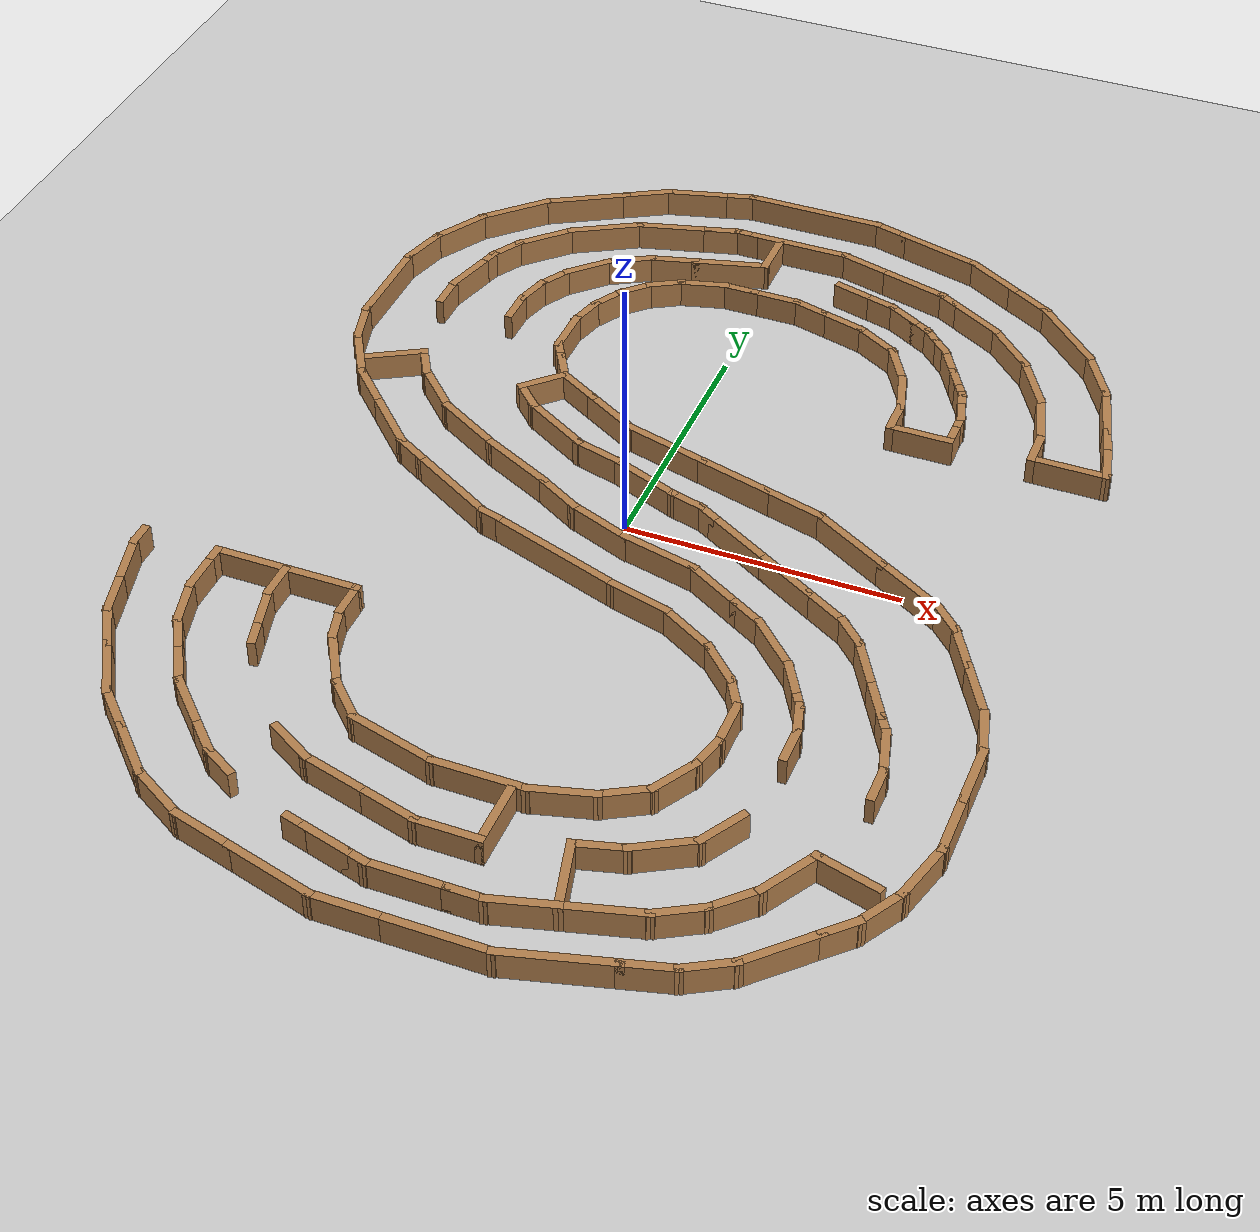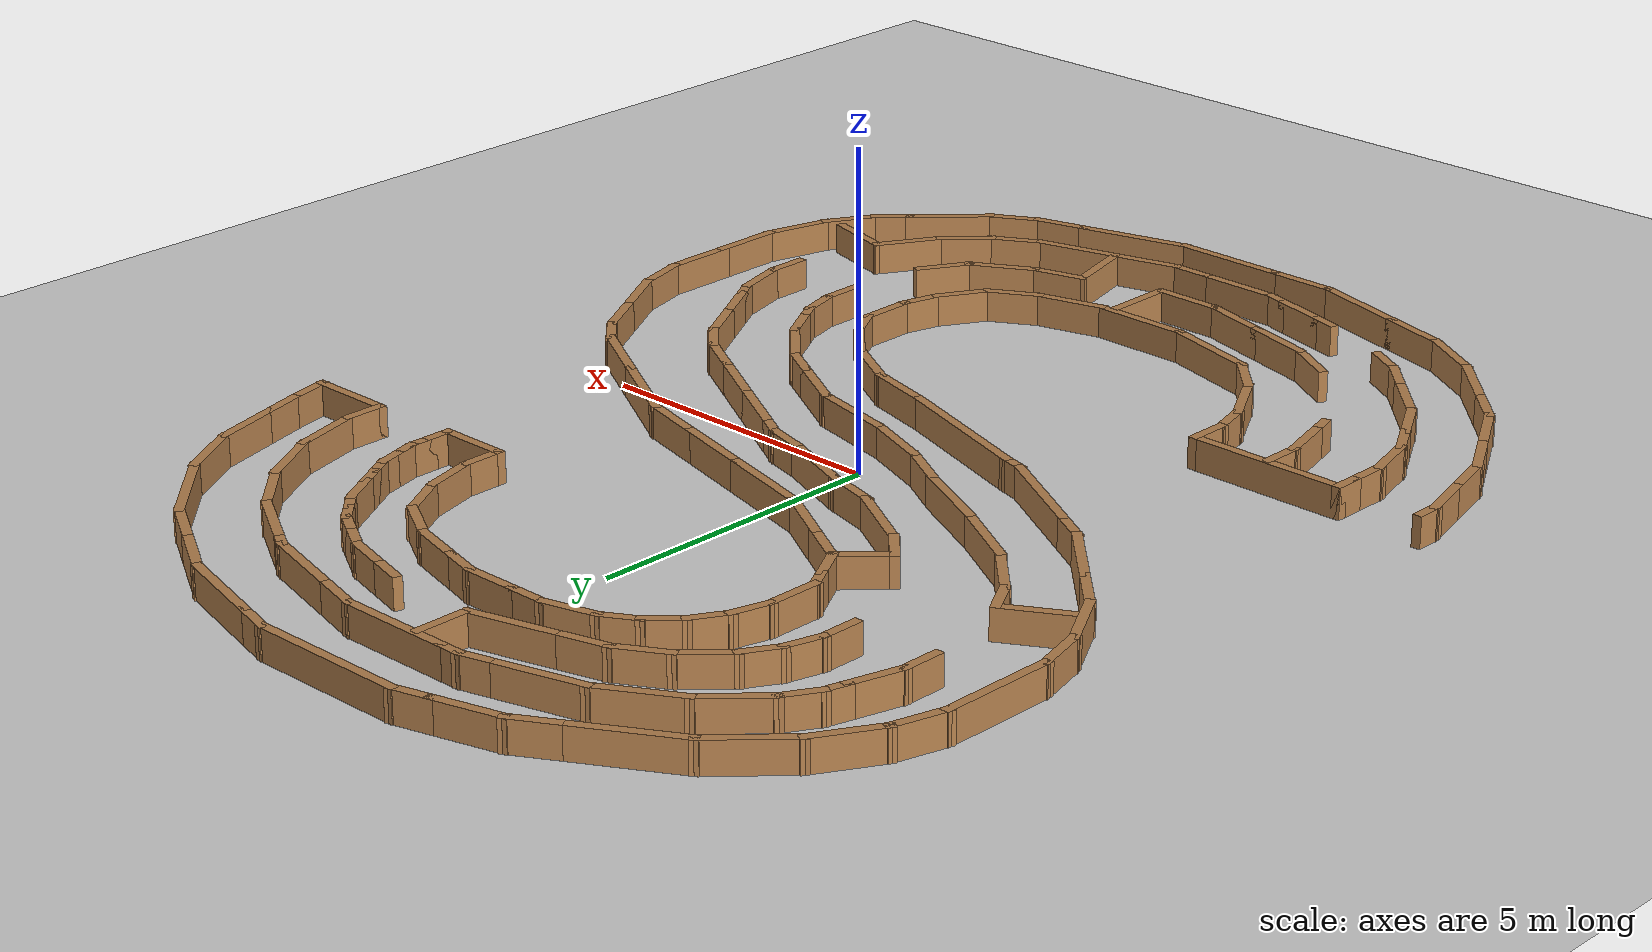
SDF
<sdf version="1.4">
  <world name="default">

    <scene>
      <ambient>0.4 0.4 0.4 1</ambient>
      <background>0.7 0.7 0.7 1</background>
      <shadows>true</shadows>
    </scene>

    <!-- A global light source -->
    <include>
      <uri>model://sun</uri>
    </include>

    <!-- A ground plane -->
    <include>
      <uri>model://ground_plane</uri>
    </include>

    <!-- my maze -->
    <include>
      <uri>model://maze-s</uri>
    </include>

    <physics type="ode">
      <real_time_update_rate>1000.0</real_time_update_rate>
      <max_step_size>0.001</max_step_size>
      <real_time_factor>1</real_time_factor>
      <ode>
        <solver>
          <type>quick</type>
          <iters>150</iters>
          <precon_iters>0</precon_iters>
          <sor>1.400000</sor>
          <use_dynamic_moi_rescaling>1</use_dynamic_moi_rescaling>
        </solver>
        <constraints>
          <cfm>0.00001</cfm>
          <erp>0.2</erp>
          <contact_max_correcting_vel>2000.000000</contact_max_correcting_vel>
          <contact_surface_layer>0.01000</contact_surface_layer>
        </constraints>
      </ode>
    </physics>
  </world>

</sdf>

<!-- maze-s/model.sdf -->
<sdf version='1.6'>
  <model name='maze-S'>
    <pose frame=''>0.044345 -0.028084 0 0 -0 0</pose>
    <link name='Wall_167'>
      <collision name='Wall_167_Collision'>
        <geometry>
          <box>
            <size>1.5 0.15 0.5</size>
          </box>
        </geometry>
        <pose frame=''>0 0 0.25 0 -0 0</pose>
      </collision>
      <visual name='Wall_167_Visual'>
        <pose frame=''>0 0 0.25 0 -0 0</pose>
        <geometry>
          <box>
            <size>1.5 0.15 0.5</size>
          </box>
        </geometry>
        <material>
          <script>
            <uri>file://media/materials/scripts/gazebo.material</uri>
            <name>Gazebo/Wood</name>
          </script>
          <ambient>1 1 1 1</ambient>
        </material>
        <meta>
          <layer>0</layer>
        </meta>
      </visual>
      <pose frame=''>6.75824 3.91414 0 0 -0 3.14159</pose>
    </link>
    <link name='Wall_168'>
      <collision name='Wall_168_Collision'>
        <geometry>
          <box>
            <size>0.75 0.15 0.5</size>
          </box>
        </geometry>
        <pose frame=''>0 0 0.25 0 -0 0</pose>
      </collision>
      <visual name='Wall_168_Visual'>
        <pose frame=''>0 0 0.25 0 -0 0</pose>
        <geometry>
          <box>
            <size>0.75 0.15 0.5</size>
          </box>
        </geometry>
        <material>
          <script>
            <uri>file://media/materials/scripts/gazebo.material</uri>
            <name>Gazebo/Wood</name>
          </script>
          <ambient>1 1 1 1</ambient>
        </material>
        <meta>
          <layer>0</layer>
        </meta>
      </visual>
      <pose frame=''>6.08324 4.21414 0 0 -0 1.5708</pose>
    </link>
    <link name='Wall_169'>
      <collision name='Wall_169_Collision'>
        <geometry>
          <box>
            <size>1.25 0.15 0.5</size>
          </box>
        </geometry>
        <pose frame=''>0 0 0.25 0 -0 0</pose>
      </collision>
      <visual name='Wall_169_Visual'>
        <pose frame=''>0 0 0.25 0 -0 0</pose>
        <geometry>
          <box>
            <size>1.25 0.15 0.5</size>
          </box>
        </geometry>
        <material>
          <script>
            <uri>file://media/materials/scripts/gazebo.material</uri>
            <name>Gazebo/Wood</name>
          </script>
          <ambient>1 1 1 1</ambient>
        </material>
        <meta>
          <layer>0</layer>
        </meta>
      </visual>
      <pose frame=''>5.94089 5.0454 0 0 -0 1.8326</pose>
    </link>
    <link name='Wall_170'>
      <collision name='Wall_170_Collision'>
        <geometry>
          <box>
            <size>1.25 0.15 0.5</size>
          </box>
        </geometry>
        <pose frame=''>0 0 0.25 0 -0 0</pose>
      </collision>
      <visual name='Wall_170_Visual'>
        <pose frame=''>0 0 0.25 0 -0 0</pose>
        <geometry>
          <box>
            <size>1.25 0.15 0.5</size>
          </box>
        </geometry>
        <material>
          <script>
            <uri>file://media/materials/scripts/gazebo.material</uri>
            <name>Gazebo/Wood</name>
          </script>
          <ambient>1 1 1 1</ambient>
        </material>
        <meta>
          <layer>0</layer>
        </meta>
      </visual>
      <pose frame=''>5.52354 6.05297 0 0 -0 2.0944</pose>
    </link>
    <link name='Wall_171'>
      <collision name='Wall_171_Collision'>
        <geometry>
          <box>
            <size>1.25 0.15 0.5</size>
          </box>
        </geometry>
        <pose frame=''>0 0 0.25 0 -0 0</pose>
      </collision>
      <visual name='Wall_171_Visual'>
        <pose frame=''>0 0 0.25 0 -0 0</pose>
        <geometry>
          <box>
            <size>1.25 0.15 0.5</size>
          </box>
        </geometry>
        <material>
          <script>
            <uri>file://media/materials/scripts/gazebo.material</uri>
            <name>Gazebo/Wood</name>
          </script>
          <ambient>1 1 1 1</ambient>
        </material>
        <meta>
          <layer>0</layer>
        </meta>
      </visual>
      <pose frame=''>4.85963 6.91819 0 0 -0 2.35619</pose>
    </link>
    <link name='Wall_172'>
      <collision name='Wall_172_Collision'>
        <geometry>
          <box>
            <size>1.25 0.15 0.5</size>
          </box>
        </geometry>
        <pose frame=''>0 0 0.25 0 -0 0</pose>
      </collision>
      <visual name='Wall_172_Visual'>
        <pose frame=''>0 0 0.25 0 -0 0</pose>
        <geometry>
          <box>
            <size>1.25 0.15 0.5</size>
          </box>
        </geometry>
        <material>
          <script>
            <uri>file://media/materials/scripts/gazebo.material</uri>
            <name>Gazebo/Wood</name>
          </script>
          <ambient>1 1 1 1</ambient>
        </material>
        <meta>
          <layer>0</layer>
        </meta>
      </visual>
      <pose frame=''>3.99441 7.5821 0 0 -0 2.61799</pose>
    </link>
    <link name='Wall_173'>
      <collision name='Wall_173_Collision'>
        <geometry>
          <box>
            <size>0.5 0.15 0.5</size>
          </box>
        </geometry>
        <pose frame=''>0 0 0.25 0 -0 0</pose>
      </collision>
      <visual name='Wall_173_Visual'>
        <pose frame=''>0 0 0.25 0 -0 0</pose>
        <geometry>
          <box>
            <size>0.5 0.15 0.5</size>
          </box>
        </geometry>
        <material>
          <script>
            <uri>file://media/materials/scripts/gazebo.material</uri>
            <name>Gazebo/Wood</name>
          </script>
          <ambient>1 1 1 1</ambient>
        </material>
        <meta>
          <layer>0</layer>
        </meta>
      </visual>
      <pose frame=''>3.36654 7.9446 0 0 -0 2.61799</pose>
    </link>
    <link name='Wall_174'>
      <collision name='Wall_174_Collision'>
        <geometry>
          <box>
            <size>1.5 0.15 0.5</size>
          </box>
        </geometry>
        <pose frame=''>0 0 0.25 0 -0 0</pose>
      </collision>
      <visual name='Wall_174_Visual'>
        <pose frame=''>0 0 0.25 0 -0 0</pose>
        <geometry>
          <box>
            <size>1.5 0.15 0.5</size>
          </box>
        </geometry>
        <material>
          <script>
            <uri>file://media/materials/scripts/gazebo.material</uri>
            <name>Gazebo/Wood</name>
          </script>
          <ambient>1 1 1 1</ambient>
        </material>
        <meta>
          <layer>0</layer>
        </meta>
      </visual>
      <pose frame=''>2.56299 8.2068 0 0 -0 2.87979</pose>
    </link>
    <link name='Wall_175'>
      <collision name='Wall_175_Collision'>
        <geometry>
          <box>
            <size>1 0.15 0.5</size>
          </box>
        </geometry>
        <pose frame=''>0 0 0.25 0 -0 0</pose>
      </collision>
      <visual name='Wall_175_Visual'>
        <pose frame=''>0 0 0.25 0 -0 0</pose>
        <geometry>
          <box>
            <size>1 0.15 0.5</size>
          </box>
        </geometry>
        <material>
          <script>
            <uri>file://media/materials/scripts/gazebo.material</uri>
            <name>Gazebo/Wood</name>
          </script>
          <ambient>1 1 1 1</ambient>
        </material>
        <meta>
          <layer>0</layer>
        </meta>
      </visual>
      <pose frame=''>1.50047 8.4915 0 0 -0 2.87979</pose>
    </link>
    <link name='Wall_176'>
      <collision name='Wall_176_Collision'>
        <geometry>
          <box>
            <size>2 0.15 0.5</size>
          </box>
        </geometry>
        <pose frame=''>0 0 0.25 0 -0 0</pose>
      </collision>
      <visual name='Wall_176_Visual'>
        <pose frame=''>0 0 0.25 0 -0 0</pose>
        <geometry>
          <box>
            <size>2 0.15 0.5</size>
          </box>
        </geometry>
        <material>
          <script>
            <uri>file://media/materials/scripts/gazebo.material</uri>
            <name>Gazebo/Wood</name>
          </script>
          <ambient>1 1 1 1</ambient>
        </material>
        <meta>
          <layer>0</layer>
        </meta>
      </visual>
      <pose frame=''>0.164949 8.6015 0 0 -0 3.14159</pose>
    </link>
    <link name='Wall_177'>
      <collision name='Wall_177_Collision'>
        <geometry>
          <box>
            <size>0.5 0.15 0.5</size>
          </box>
        </geometry>
        <pose frame=''>0 0 0.25 0 -0 0</pose>
      </collision>
      <visual name='Wall_177_Visual'>
        <pose frame=''>0 0 0.25 0 -0 0</pose>
        <geometry>
          <box>
            <size>0.5 0.15 0.5</size>
          </box>
        </geometry>
        <material>
          <script>
            <uri>file://media/materials/scripts/gazebo.material</uri>
            <name>Gazebo/Wood</name>
          </script>
          <ambient>1 1 1 1</ambient>
        </material>
        <meta>
          <layer>0</layer>
        </meta>
      </visual>
      <pose frame=''>-0.935051 8.6015 0 0 -0 3.14159</pose>
    </link>
    <link name='Wall_178'>
      <collision name='Wall_178_Collision'>
        <geometry>
          <box>
            <size>0.75 0.15 0.5</size>
          </box>
        </geometry>
        <pose frame=''>0 0 0.25 0 -0 0</pose>
      </collision>
      <visual name='Wall_178_Visual'>
        <pose frame=''>0 0 0.25 0 -0 0</pose>
        <geometry>
          <box>
            <size>0.75 0.15 0.5</size>
          </box>
        </geometry>
        <material>
          <script>
            <uri>file://media/materials/scripts/gazebo.material</uri>
            <name>Gazebo/Wood</name>
          </script>
          <ambient>1 1 1 1</ambient>
        </material>
        <meta>
          <layer>0</layer>
        </meta>
      </visual>
      <pose frame=''>-1.39983 8.52386 0 0 -0 -2.87979</pose>
    </link>
    <link name='Wall_179'>
      <collision name='Wall_179_Collision'>
        <geometry>
          <box>
            <size>1.5 0.15 0.5</size>
          </box>
        </geometry>
        <pose frame=''>0 0 0.25 0 -0 0</pose>
      </collision>
      <visual name='Wall_179_Visual'>
        <pose frame=''>0 0 0.25 0 -0 0</pose>
        <geometry>
          <box>
            <size>1.5 0.15 0.5</size>
          </box>
        </geometry>
        <material>
          <script>
            <uri>file://media/materials/scripts/gazebo.material</uri>
            <name>Gazebo/Wood</name>
          </script>
          <ambient>1 1 1 1</ambient>
        </material>
        <meta>
          <layer>0</layer>
        </meta>
      </visual>
      <pose frame=''>-2.34161 8.27151 0 0 -0 -2.87979</pose>
    </link>
    <link name='Wall_180'>
      <collision name='Wall_180_Collision'>
        <geometry>
          <box>
            <size>1.5 0.15 0.5</size>
          </box>
        </geometry>
        <pose frame=''>0 0 0.25 0 -0 0</pose>
      </collision>
      <visual name='Wall_180_Visual'>
        <pose frame=''>0 0 0.25 0 -0 0</pose>
        <geometry>
          <box>
            <size>1.5 0.15 0.5</size>
          </box>
        </geometry>
        <material>
          <script>
            <uri>file://media/materials/scripts/gazebo.material</uri>
            <name>Gazebo/Wood</name>
          </script>
          <ambient>1 1 1 1</ambient>
        </material>
        <meta>
          <layer>0</layer>
        </meta>
      </visual>
      <pose frame=''>-3.57817 7.75931 0 0 -0 -2.61799</pose>
    </link>
    <link name='Wall_181'>
      <collision name='Wall_181_Collision'>
        <geometry>
          <box>
            <size>1.25 0.15 0.5</size>
          </box>
        </geometry>
        <pose frame=''>0 0 0.25 0 -0 0</pose>
      </collision>
      <visual name='Wall_181_Visual'>
        <pose frame=''>0 0 0.25 0 -0 0</pose>
        <geometry>
          <box>
            <size>1.25 0.15 0.5</size>
          </box>
        </geometry>
        <material>
          <script>
            <uri>file://media/materials/scripts/gazebo.material</uri>
            <name>Gazebo/Wood</name>
          </script>
          <ambient>1 1 1 1</ambient>
        </material>
        <meta>
          <layer>0</layer>
        </meta>
      </visual>
      <pose frame=''>-4.55165 7.0329 0 0 -0 -2.35619</pose>
    </link>
    <link name='Wall_182'>
      <collision name='Wall_182_Collision'>
        <geometry>
          <box>
            <size>0.75 0.15 0.5</size>
          </box>
        </geometry>
        <pose frame=''>0 0 0.25 0 -0 0</pose>
      </collision>
      <visual name='Wall_182_Visual'>
        <pose frame=''>0 0 0.25 0 -0 0</pose>
        <geometry>
          <box>
            <size>0.75 0.15 0.5</size>
          </box>
        </geometry>
        <material>
          <script>
            <uri>file://media/materials/scripts/gazebo.material</uri>
            <name>Gazebo/Wood</name>
          </script>
          <ambient>1 1 1 1</ambient>
        </material>
        <meta>
          <layer>0</layer>
        </meta>
      </visual>
      <pose frame=''>-5.09056 6.38418 0 0 -0 -2.0944</pose>
    </link>
    <link name='Wall_183'>
      <collision name='Wall_183_Collision'>
        <geometry>
          <box>
            <size>0.5 0.15 0.5</size>
          </box>
        </geometry>
        <pose frame=''>0 0 0.25 0 -0 0</pose>
      </collision>
      <visual name='Wall_183_Visual'>
        <pose frame=''>0 0 0.25 0 -0 0</pose>
        <geometry>
          <box>
            <size>0.5 0.15 0.5</size>
          </box>
        </geometry>
        <material>
          <script>
            <uri>file://media/materials/scripts/gazebo.material</uri>
            <name>Gazebo/Wood</name>
          </script>
          <ambient>1 1 1 1</ambient>
        </material>
        <meta>
          <layer>0</layer>
        </meta>
      </visual>
      <pose frame=''>-5.28585 5.95533 0 0 -0 -1.8326</pose>
    </link>
    <link name='Wall_184'>
      <collision name='Wall_184_Collision'>
        <geometry>
          <box>
            <size>1 0.15 0.5</size>
          </box>
        </geometry>
        <pose frame=''>0 0 0.25 0 -0 0</pose>
      </collision>
      <visual name='Wall_184_Visual'>
        <pose frame=''>0 0 0.25 0 -0 0</pose>
        <geometry>
          <box>
            <size>1 0.15 0.5</size>
          </box>
        </geometry>
        <material>
          <script>
            <uri>file://media/materials/scripts/gazebo.material</uri>
            <name>Gazebo/Wood</name>
          </script>
          <ambient>1 1 1 1</ambient>
        </material>
        <meta>
          <layer>0</layer>
        </meta>
      </visual>
      <pose frame=''>-5.44114 5.37578 0 0 -0 -1.8326</pose>
    </link>
    <link name='Wall_185'>
      <collision name='Wall_185_Collision'>
        <geometry>
          <box>
            <size>0.75 0.15 0.5</size>
          </box>
        </geometry>
        <pose frame=''>0 0 0.25 0 -0 0</pose>
      </collision>
      <visual name='Wall_185_Visual'>
        <pose frame=''>0 0 0.25 0 -0 0</pose>
        <geometry>
          <box>
            <size>0.75 0.15 0.5</size>
          </box>
        </geometry>
        <material>
          <script>
            <uri>file://media/materials/scripts/gazebo.material</uri>
            <name>Gazebo/Wood</name>
          </script>
          <ambient>1 1 1 1</ambient>
        </material>
        <meta>
          <layer>0</layer>
        </meta>
      </visual>
      <pose frame=''>-5.55114 4.66526 0 0 -0 -1.5708</pose>
    </link>
    <link name='Wall_187'>
      <collision name='Wall_187_Collision'>
        <geometry>
          <box>
            <size>0.75 0.15 0.5</size>
          </box>
        </geometry>
        <pose frame=''>0 0 0.25 0 -0 0</pose>
      </collision>
      <visual name='Wall_187_Visual'>
        <pose frame=''>0 0 0.25 0 -0 0</pose>
        <geometry>
          <box>
            <size>0.75 0.15 0.5</size>
          </box>
        </geometry>
        <material>
          <script>
            <uri>file://media/materials/scripts/gazebo.material</uri>
            <name>Gazebo/Wood</name>
          </script>
          <ambient>1 1 1 1</ambient>
        </material>
        <meta>
          <layer>0</layer>
        </meta>
      </visual>
      <pose frame=''>-4.15063 4.7033 0 0 -0 1.5708</pose>
    </link>
    <link name='Wall_188'>
      <collision name='Wall_188_Collision'>
        <geometry>
          <box>
            <size>0.75 0.15 0.5</size>
          </box>
        </geometry>
        <pose frame=''>0 0 0.25 0 -0 0</pose>
      </collision>
      <visual name='Wall_188_Visual'>
        <pose frame=''>0 0 0.25 0 -0 0</pose>
        <geometry>
          <box>
            <size>0.75 0.15 0.5</size>
          </box>
        </geometry>
        <material>
          <script>
            <uri>file://media/materials/scripts/gazebo.material</uri>
            <name>Gazebo/Wood</name>
          </script>
          <ambient>1 1 1 1</ambient>
        </material>
        <meta>
          <layer>0</layer>
        </meta>
      </visual>
      <pose frame=''>-4.07298 5.29308 0 0 -0 1.309</pose>
    </link>
    <link name='Wall_189'>
      <collision name='Wall_189_Collision'>
        <geometry>
          <box>
            <size>0.75 0.15 0.5</size>
          </box>
        </geometry>
        <pose frame=''>0 0 0.25 0 -0 0</pose>
      </collision>
      <visual name='Wall_189_Visual'>
        <pose frame=''>0 0 0.25 0 -0 0</pose>
        <geometry>
          <box>
            <size>0.75 0.15 0.5</size>
          </box>
        </geometry>
        <material>
          <script>
            <uri>file://media/materials/scripts/gazebo.material</uri>
            <name>Gazebo/Wood</name>
          </script>
          <ambient>1 1 1 1</ambient>
        </material>
        <meta>
          <layer>0</layer>
        </meta>
      </visual>
      <pose frame=''>-3.84534 5.84266 0 0 -0 1.0472</pose>
    </link>
    <link name='Wall_190'>
      <collision name='Wall_190_Collision'>
        <geometry>
          <box>
            <size>1 0.15 0.5</size>
          </box>
        </geometry>
        <pose frame=''>0 0 0.25 0 -0 0</pose>
      </collision>
      <visual name='Wall_190_Visual'>
        <pose frame=''>0 0 0.25 0 -0 0</pose>
        <geometry>
          <box>
            <size>1 0.15 0.5</size>
          </box>
        </geometry>
        <material>
          <script>
            <uri>file://media/materials/scripts/gazebo.material</uri>
            <name>Gazebo/Wood</name>
          </script>
          <ambient>1 1 1 1</ambient>
        </material>
        <meta>
          <layer>0</layer>
        </meta>
      </visual>
      <pose frame=''>-3.39482 6.40299 0 0 -0 0.785398</pose>
    </link>
    <link name='Wall_191'>
      <collision name='Wall_191_Collision'>
        <geometry>
          <box>
            <size>1 0.15 0.5</size>
          </box>
        </geometry>
        <pose frame=''>0 0 0.25 0 -0 0</pose>
      </collision>
      <visual name='Wall_191_Visual'>
        <pose frame=''>0 0 0.25 0 -0 0</pose>
        <geometry>
          <box>
            <size>1 0.15 0.5</size>
          </box>
        </geometry>
        <material>
          <script>
            <uri>file://media/materials/scripts/gazebo.material</uri>
            <name>Gazebo/Wood</name>
          </script>
          <ambient>1 1 1 1</ambient>
        </material>
        <meta>
          <layer>0</layer>
        </meta>
      </visual>
      <pose frame=''>-2.72623 6.91601 0 0 -0 0.523599</pose>
    </link>
    <link name='Wall_192'>
      <collision name='Wall_192_Collision'>
        <geometry>
          <box>
            <size>1 0.15 0.5</size>
          </box>
        </geometry>
        <pose frame=''>0 0 0.25 0 -0 0</pose>
      </collision>
      <visual name='Wall_192_Visual'>
        <pose frame=''>0 0 0.25 0 -0 0</pose>
        <geometry>
          <box>
            <size>1 0.15 0.5</size>
          </box>
        </geometry>
        <material>
          <script>
            <uri>file://media/materials/scripts/gazebo.material</uri>
            <name>Gazebo/Wood</name>
          </script>
          <ambient>1 1 1 1</ambient>
        </material>
        <meta>
          <layer>0</layer>
        </meta>
      </visual>
      <pose frame=''>-1.94765 7.23851 0 0 -0 0.261799</pose>
    </link>
    <link name='Wall_193'>
      <collision name='Wall_193_Collision'>
        <geometry>
          <box>
            <size>1.5 0.15 0.5</size>
          </box>
        </geometry>
        <pose frame=''>0 0 0.25 0 -0 0</pose>
      </collision>
      <visual name='Wall_193_Visual'>
        <pose frame=''>0 0 0.25 0 -0 0</pose>
        <geometry>
          <box>
            <size>1.5 0.15 0.5</size>
          </box>
        </geometry>
        <material>
          <script>
            <uri>file://media/materials/scripts/gazebo.material</uri>
            <name>Gazebo/Wood</name>
          </script>
          <ambient>1 1 1 1</ambient>
        </material>
        <meta>
          <layer>0</layer>
        </meta>
      </visual>
      <pose frame=''>-0.885137 7.52321 0 0 -0 0.261799</pose>
    </link>
    <link name='Wall_194'>
      <collision name='Wall_194_Collision'>
        <geometry>
          <box>
            <size>1 0.15 0.5</size>
          </box>
        </geometry>
        <pose frame=''>0 0 0.25 0 -0 0</pose>
      </collision>
      <visual name='Wall_194_Visual'>
        <pose frame=''>0 0 0.25 0 -0 0</pose>
        <geometry>
          <box>
            <size>1 0.15 0.5</size>
          </box>
        </geometry>
        <material>
          <script>
            <uri>file://media/materials/scripts/gazebo.material</uri>
            <name>Gazebo/Wood</name>
          </script>
          <ambient>1 1 1 1</ambient>
        </material>
        <meta>
          <layer>0</layer>
        </meta>
      </visual>
      <pose frame=''>-0.233137 8.12291 0 0 -0 1.5708</pose>
    </link>
    <link name='Wall_196'>
      <collision name='Wall_196_Collision'>
        <geometry>
          <box>
            <size>0.75 0.15 0.5</size>
          </box>
        </geometry>
        <pose frame=''>0 0 0.25 0 -0 0</pose>
      </collision>
      <visual name='Wall_196_Visual'>
        <pose frame=''>0 0 0.25 0 -0 0</pose>
        <geometry>
          <box>
            <size>0.75 0.15 0.5</size>
          </box>
        </geometry>
        <material>
          <script>
            <uri>file://media/materials/scripts/gazebo.material</uri>
            <name>Gazebo/Wood</name>
          </script>
          <ambient>1 1 1 1</ambient>
        </material>
        <meta>
          <layer>0</layer>
        </meta>
      </visual>
      <pose frame=''>1.59015 7.55715 0 0 -0 -0.261799</pose>
    </link>
    <link name='Wall_197'>
      <collision name='Wall_197_Collision'>
        <geometry>
          <box>
            <size>0.75 0.15 0.5</size>
          </box>
        </geometry>
        <pose frame=''>0 0 0.25 0 -0 0</pose>
      </collision>
      <visual name='Wall_197_Visual'>
        <pose frame=''>0 0 0.25 0 -0 0</pose>
        <geometry>
          <box>
            <size>0.75 0.15 0.5</size>
          </box>
        </geometry>
        <material>
          <script>
            <uri>file://media/materials/scripts/gazebo.material</uri>
            <name>Gazebo/Wood</name>
          </script>
          <ambient>1 1 1 1</ambient>
        </material>
        <meta>
          <layer>0</layer>
        </meta>
      </visual>
      <pose frame=''>2.16971 7.40186 0 0 -0 -0.261799</pose>
    </link>
    <link name='Wall_198'>
      <collision name='Wall_198_Collision'>
        <geometry>
          <box>
            <size>0.75 0.15 0.5</size>
          </box>
        </geometry>
        <pose frame=''>0 0 0.25 0 -0 0</pose>
      </collision>
      <visual name='Wall_198_Visual'>
        <pose frame=''>0 0 0.25 0 -0 0</pose>
        <geometry>
          <box>
            <size>0.75 0.15 0.5</size>
          </box>
        </geometry>
        <material>
          <script>
            <uri>file://media/materials/scripts/gazebo.material</uri>
            <name>Gazebo/Wood</name>
          </script>
          <ambient>1 1 1 1</ambient>
        </material>
        <meta>
          <layer>0</layer>
        </meta>
      </visual>
      <pose frame=''>2.71929 7.17422 0 0 -0 -0.523599</pose>
    </link>
    <link name='Wall_199'>
      <collision name='Wall_199_Collision'>
        <geometry>
          <box>
            <size>0.5 0.15 0.5</size>
          </box>
        </geometry>
        <pose frame=''>0 0 0.25 0 -0 0</pose>
      </collision>
      <visual name='Wall_199_Visual'>
        <pose frame=''>0 0 0.25 0 -0 0</pose>
        <geometry>
          <box>
            <size>0.5 0.15 0.5</size>
          </box>
        </geometry>
        <material>
          <script>
            <uri>file://media/materials/scripts/gazebo.material</uri>
            <name>Gazebo/Wood</name>
          </script>
          <ambient>1 1 1 1</ambient>
        </material>
        <meta>
          <layer>0</layer>
        </meta>
      </visual>
      <pose frame=''>3.13065 6.93672 0 0 -0 -0.523599</pose>
    </link>
    <link name='Wall_200'>
      <collision name='Wall_200_Collision'>
        <geometry>
          <box>
            <size>0.5 0.15 0.5</size>
          </box>
        </geometry>
        <pose frame=''>0 0 0.25 0 -0 0</pose>
      </collision>
      <visual name='Wall_200_Visual'>
        <pose frame=''>0 0 0.25 0 -0 0</pose>
        <geometry>
          <box>
            <size>0.5 0.15 0.5</size>
          </box>
        </geometry>
        <material>
          <script>
            <uri>file://media/materials/scripts/gazebo.material</uri>
            <name>Gazebo/Wood</name>
          </script>
          <ambient>1 1 1 1</ambient>
        </material>
        <meta>
          <layer>0</layer>
        </meta>
      </visual>
      <pose frame=''>3.40595 6.72547 0 0 -0 -0.785398</pose>
    </link>
    <link name='Wall_201'>
      <collision name='Wall_201_Collision'>
        <geometry>
          <box>
            <size>0.5 0.15 0.5</size>
          </box>
        </geometry>
        <pose frame=''>0 0 0.25 0 -0 0</pose>
      </collision>
      <visual name='Wall_201_Visual'>
        <pose frame=''>0 0 0.25 0 -0 0</pose>
        <geometry>
          <box>
            <size>0.5 0.15 0.5</size>
          </box>
        </geometry>
        <material>
          <script>
            <uri>file://media/materials/scripts/gazebo.material</uri>
            <name>Gazebo/Wood</name>
          </script>
          <ambient>1 1 1 1</ambient>
        </material>
        <meta>
          <layer>0</layer>
        </meta>
      </visual>
      <pose frame=''>3.65344 6.47799 0 0 -0 -0.785398</pose>
    </link>
    <link name='Wall_202'>
      <collision name='Wall_202_Collision'>
        <geometry>
          <box>
            <size>0.75 0.15 0.5</size>
          </box>
        </geometry>
        <pose frame=''>0 0 0.25 0 -0 0</pose>
      </collision>
      <visual name='Wall_202_Visual'>
        <pose frame=''>0 0 0.25 0 -0 0</pose>
        <geometry>
          <box>
            <size>0.75 0.15 0.5</size>
          </box>
        </geometry>
        <material>
          <script>
            <uri>file://media/materials/scripts/gazebo.material</uri>
            <name>Gazebo/Wood</name>
          </script>
          <ambient>1 1 1 1</ambient>
        </material>
        <meta>
          <layer>0</layer>
        </meta>
      </visual>
      <pose frame=''>3.92718 6.09443 0 0 -0 -1.0472</pose>
    </link>
    <link name='Wall_203'>
      <collision name='Wall_203_Collision'>
        <geometry>
          <box>
            <size>0.5 0.15 0.5</size>
          </box>
        </geometry>
        <pose frame=''>0 0 0.25 0 -0 0</pose>
      </collision>
      <visual name='Wall_203_Visual'>
        <pose frame=''>0 0 0.25 0 -0 0</pose>
        <geometry>
          <box>
            <size>0.5 0.15 0.5</size>
          </box>
        </geometry>
        <material>
          <script>
            <uri>file://media/materials/scripts/gazebo.material</uri>
            <name>Gazebo/Wood</name>
          </script>
          <ambient>1 1 1 1</ambient>
        </material>
        <meta>
          <layer>0</layer>
        </meta>
      </visual>
      <pose frame=''>4.16468 5.68307 0 0 -0 -1.0472</pose>
    </link>
    <link name='Wall_204'>
      <collision name='Wall_204_Collision'>
        <geometry>
          <box>
            <size>0.5 0.15 0.5</size>
          </box>
        </geometry>
        <pose frame=''>0 0 0.25 0 -0 0</pose>
      </collision>
      <visual name='Wall_204_Visual'>
        <pose frame=''>0 0 0.25 0 -0 0</pose>
        <geometry>
          <box>
            <size>0.5 0.15 0.5</size>
          </box>
        </geometry>
        <material>
          <script>
            <uri>file://media/materials/scripts/gazebo.material</uri>
            <name>Gazebo/Wood</name>
          </script>
          <ambient>1 1 1 1</ambient>
        </material>
        <meta>
          <layer>0</layer>
        </meta>
      </visual>
      <pose frame=''>4.33968 5.37996 0 0 -0 -1.0472</pose>
    </link>
    <link name='Wall_205'>
      <collision name='Wall_205_Collision'>
        <geometry>
          <box>
            <size>0.5 0.15 0.5</size>
          </box>
        </geometry>
        <pose frame=''>0 0 0.25 0 -0 0</pose>
      </collision>
      <visual name='Wall_205_Visual'>
        <pose frame=''>0 0 0.25 0 -0 0</pose>
        <geometry>
          <box>
            <size>0.5 0.15 0.5</size>
          </box>
        </geometry>
        <material>
          <script>
            <uri>file://media/materials/scripts/gazebo.material</uri>
            <name>Gazebo/Wood</name>
          </script>
          <ambient>1 1 1 1</ambient>
        </material>
        <meta>
          <layer>0</layer>
        </meta>
      </visual>
      <pose frame=''>4.47248 5.05937 0 0 -0 -1.309</pose>
    </link>
    <link name='Wall_206'>
      <collision name='Wall_206_Collision'>
        <geometry>
          <box>
            <size>0.5 0.15 0.5</size>
          </box>
        </geometry>
        <pose frame=''>0 0 0.25 0 -0 0</pose>
      </collision>
      <visual name='Wall_206_Visual'>
        <pose frame=''>0 0 0.25 0 -0 0</pose>
        <geometry>
          <box>
            <size>0.5 0.15 0.5</size>
          </box>
        </geometry>
        <material>
          <script>
            <uri>file://media/materials/scripts/gazebo.material</uri>
            <name>Gazebo/Wood</name>
          </script>
          <ambient>1 1 1 1</ambient>
        </material>
        <meta>
          <layer>0</layer>
        </meta>
      </visual>
      <pose frame=''>4.56306 4.7213 0 0 -0 -1.309</pose>
    </link>
    <link name='Wall_207'>
      <collision name='Wall_207_Collision'>
        <geometry>
          <box>
            <size>0.5 0.15 0.5</size>
          </box>
        </geometry>
        <pose frame=''>0 0 0.25 0 -0 0</pose>
      </collision>
      <visual name='Wall_207_Visual'>
        <pose frame=''>0 0 0.25 0 -0 0</pose>
        <geometry>
          <box>
            <size>0.5 0.15 0.5</size>
          </box>
        </geometry>
        <material>
          <script>
            <uri>file://media/materials/scripts/gazebo.material</uri>
            <name>Gazebo/Wood</name>
          </script>
          <ambient>1 1 1 1</ambient>
        </material>
        <meta>
          <layer>0</layer>
        </meta>
      </visual>
      <pose frame=''>4.60836 4.37726 0 0 -0 -1.5708</pose>
    </link>
    <link name='Wall_208'>
      <collision name='Wall_208_Collision'>
        <geometry>
          <box>
            <size>0.5 0.15 0.5</size>
          </box>
        </geometry>
        <pose frame=''>0 0 0.25 0 -0 0</pose>
      </collision>
      <visual name='Wall_208_Visual'>
        <pose frame=''>0 0 0.25 0 -0 0</pose>
        <geometry>
          <box>
            <size>0.5 0.15 0.5</size>
          </box>
        </geometry>
        <material>
          <script>
            <uri>file://media/materials/scripts/gazebo.material</uri>
            <name>Gazebo/Wood</name>
          </script>
          <ambient>1 1 1 1</ambient>
        </material>
        <meta>
          <layer>0</layer>
        </meta>
      </visual>
      <pose frame=''>4.60836 4.02726 0 0 -0 -1.5708</pose>
    </link>
    <link name='Wall_209'>
      <collision name='Wall_209_Collision'>
        <geometry>
          <box>
            <size>1.25 0.15 0.5</size>
          </box>
        </geometry>
        <pose frame=''>0 0 0.25 0 -0 0</pose>
      </collision>
      <visual name='Wall_209_Visual'>
        <pose frame=''>0 0 0.25 0 -0 0</pose>
        <geometry>
          <box>
            <size>1.25 0.15 0.5</size>
          </box>
        </geometry>
        <material>
          <script>
            <uri>file://media/materials/scripts/gazebo.material</uri>
            <name>Gazebo/Wood</name>
          </script>
          <ambient>1 1 1 1</ambient>
        </material>
        <meta>
          <layer>0</layer>
        </meta>
      </visual>
      <pose frame=''>4.05835 3.85226 0 0 -0 3.14159</pose>
    </link>
    <link name='Wall_210'>
      <collision name='Wall_210_Collision'>
        <geometry>
          <box>
            <size>0.75 0.15 0.5</size>
          </box>
        </geometry>
        <pose frame=''>0 0 0.25 0 -0 0</pose>
      </collision>
      <visual name='Wall_210_Visual'>
        <pose frame=''>0 0 0.25 0 -0 0</pose>
        <geometry>
          <box>
            <size>0.75 0.15 0.5</size>
          </box>
        </geometry>
        <material>
          <script>
            <uri>file://media/materials/scripts/gazebo.material</uri>
            <name>Gazebo/Wood</name>
          </script>
          <ambient>1 1 1 1</ambient>
        </material>
        <meta>
          <layer>0</layer>
        </meta>
      </visual>
      <pose frame=''>3.50836 4.15226 0 0 -0 1.5708</pose>
    </link>
    <link name='Wall_211'>
      <collision name='Wall_211_Collision'>
        <geometry>
          <box>
            <size>1 0.15 0.5</size>
          </box>
        </geometry>
        <pose frame=''>0 0 0.25 0 -0 0</pose>
      </collision>
      <visual name='Wall_211_Visual'>
        <pose frame=''>0 0 0.25 0 -0 0</pose>
        <geometry>
          <box>
            <size>1 0.15 0.5</size>
          </box>
        </geometry>
        <material>
          <script>
            <uri>file://media/materials/scripts/gazebo.material</uri>
            <name>Gazebo/Wood</name>
          </script>
          <ambient>1 1 1 1</ambient>
        </material>
        <meta>
          <layer>0</layer>
        </meta>
      </visual>
      <pose frame=''>3.39836 4.86278 0 0 -0 1.8326</pose>
    </link>
    <link name='Wall_212'>
      <collision name='Wall_212_Collision'>
        <geometry>
          <box>
            <size>1 0.15 0.5</size>
          </box>
        </geometry>
        <pose frame=''>0 0 0.25 0 -0 0</pose>
      </collision>
      <visual name='Wall_212_Visual'>
        <pose frame=''>0 0 0.25 0 -0 0</pose>
        <geometry>
          <box>
            <size>1 0.15 0.5</size>
          </box>
        </geometry>
        <material>
          <script>
            <uri>file://media/materials/scripts/gazebo.material</uri>
            <name>Gazebo/Wood</name>
          </script>
          <ambient>1 1 1 1</ambient>
        </material>
        <meta>
          <layer>0</layer>
        </meta>
      </visual>
      <pose frame=''>3.07586 5.64136 0 0 -0 2.0944</pose>
    </link>
    <link name='Wall_213'>
      <collision name='Wall_213_Collision'>
        <geometry>
          <box>
            <size>1 0.15 0.5</size>
          </box>
        </geometry>
        <pose frame=''>0 0 0.25 0 -0 0</pose>
      </collision>
      <visual name='Wall_213_Visual'>
        <pose frame=''>0 0 0.25 0 -0 0</pose>
        <geometry>
          <box>
            <size>1 0.15 0.5</size>
          </box>
        </geometry>
        <material>
          <script>
            <uri>file://media/materials/scripts/gazebo.material</uri>
            <name>Gazebo/Wood</name>
          </script>
          <ambient>1 1 1 1</ambient>
        </material>
        <meta>
          <layer>0</layer>
        </meta>
      </visual>
      <pose frame=''>2.4953 6.22192 0 0 -0 2.61799</pose>
    </link>
    <link name='Wall_214'>
      <collision name='Wall_214_Collision'>
        <geometry>
          <box>
            <size>1 0.15 0.5</size>
          </box>
        </geometry>
        <pose frame=''>0 0 0.25 0 -0 0</pose>
      </collision>
      <visual name='Wall_214_Visual'>
        <pose frame=''>0 0 0.25 0 -0 0</pose>
        <geometry>
          <box>
            <size>1 0.15 0.5</size>
          </box>
        </geometry>
        <material>
          <script>
            <uri>file://media/materials/scripts/gazebo.material</uri>
            <name>Gazebo/Wood</name>
          </script>
          <ambient>1 1 1 1</ambient>
        </material>
        <meta>
          <layer>0</layer>
        </meta>
      </visual>
      <pose frame=''>1.71672 6.54442 0 0 -0 2.87979</pose>
    </link>
    <link name='Wall_215'>
      <collision name='Wall_215_Collision'>
        <geometry>
          <box>
            <size>0.75 0.15 0.5</size>
          </box>
        </geometry>
        <pose frame=''>0 0 0.25 0 -0 0</pose>
      </collision>
      <visual name='Wall_215_Visual'>
        <pose frame=''>0 0 0.25 0 -0 0</pose>
        <geometry>
          <box>
            <size>0.75 0.15 0.5</size>
          </box>
        </geometry>
        <material>
          <script>
            <uri>file://media/materials/scripts/gazebo.material</uri>
            <name>Gazebo/Wood</name>
          </script>
          <ambient>1 1 1 1</ambient>
        </material>
        <meta>
          <layer>0</layer>
        </meta>
      </visual>
      <pose frame=''>1.01642 6.73206 0 0 -0 2.87979</pose>
    </link>
    <link name='Wall_216'>
      <collision name='Wall_216_Collision'>
        <geometry>
          <box>
            <size>1 0.15 0.5</size>
          </box>
        </geometry>
        <pose frame=''>0 0 0.25 0 -0 0</pose>
      </collision>
      <visual name='Wall_216_Visual'>
        <pose frame=''>0 0 0.25 0 -0 0</pose>
        <geometry>
          <box>
            <size>1 0.15 0.5</size>
          </box>
        </geometry>
        <material>
          <script>
            <uri>file://media/materials/scripts/gazebo.material</uri>
            <name>Gazebo/Wood</name>
          </script>
          <ambient>1 1 1 1</ambient>
        </material>
        <meta>
          <layer>0</layer>
        </meta>
      </visual>
      <pose frame=''>0.301645 6.80971 0 0 -0 3.14159</pose>
    </link>
    <link name='Wall_217'>
      <collision name='Wall_217_Collision'>
        <geometry>
          <box>
            <size>0.75 0.15 0.5</size>
          </box>
        </geometry>
        <pose frame=''>0 0 0.25 0 -0 0</pose>
      </collision>
      <visual name='Wall_217_Visual'>
        <pose frame=''>0 0 0.25 0 -0 0</pose>
        <geometry>
          <box>
            <size>0.75 0.15 0.5</size>
          </box>
        </geometry>
        <material>
          <script>
            <uri>file://media/materials/scripts/gazebo.material</uri>
            <name>Gazebo/Wood</name>
          </script>
          <ambient>1 1 1 1</ambient>
        </material>
        <meta>
          <layer>0</layer>
        </meta>
      </visual>
      <pose frame=''>-0.423355 6.80971 0 0 -0 3.14159</pose>
    </link>
    <link name='Wall_218'>
      <collision name='Wall_218_Collision'>
        <geometry>
          <box>
            <size>1 0.15 0.5</size>
          </box>
        </geometry>
        <pose frame=''>0 0 0.25 0 -0 0</pose>
      </collision>
      <visual name='Wall_218_Visual'>
        <pose frame=''>0 0 0.25 0 -0 0</pose>
        <geometry>
          <box>
            <size>1 0.15 0.5</size>
          </box>
        </geometry>
        <material>
          <script>
            <uri>file://media/materials/scripts/gazebo.material</uri>
            <name>Gazebo/Wood</name>
          </script>
          <ambient>1 1 1 1</ambient>
        </material>
        <meta>
          <layer>0</layer>
        </meta>
      </visual>
      <pose frame=''>-1.13387 6.69971 0 0 -0 -2.87979</pose>
    </link>
    <link name='Wall_219'>
      <collision name='Wall_219_Collision'>
        <geometry>
          <box>
            <size>0.75 0.15 0.5</size>
          </box>
        </geometry>
        <pose frame=''>0 0 0.25 0 -0 0</pose>
      </collision>
      <visual name='Wall_219_Visual'>
        <pose frame=''>0 0 0.25 0 -0 0</pose>
        <geometry>
          <box>
            <size>0.75 0.15 0.5</size>
          </box>
        </geometry>
        <material>
          <script>
            <uri>file://media/materials/scripts/gazebo.material</uri>
            <name>Gazebo/Wood</name>
          </script>
          <ambient>1 1 1 1</ambient>
        </material>
        <meta>
          <layer>0</layer>
        </meta>
      </visual>
      <pose frame=''>-1.8042 6.43971 0 0 -0 -2.61799</pose>
    </link>
    <link name='Wall_220'>
      <collision name='Wall_220_Collision'>
        <geometry>
          <box>
            <size>0.75 0.15 0.5</size>
          </box>
        </geometry>
        <pose frame=''>0 0 0.25 0 -0 0</pose>
      </collision>
      <visual name='Wall_220_Visual'>
        <pose frame=''>0 0 0.25 0 -0 0</pose>
        <geometry>
          <box>
            <size>0.75 0.15 0.5</size>
          </box>
        </geometry>
        <material>
          <script>
            <uri>file://media/materials/scripts/gazebo.material</uri>
            <name>Gazebo/Wood</name>
          </script>
          <ambient>1 1 1 1</ambient>
        </material>
        <meta>
          <layer>0</layer>
        </meta>
      </visual>
      <pose frame=''>-2.27614 6.07758 0 0 -0 -2.35619</pose>
    </link>
    <link name='Wall_221'>
      <collision name='Wall_221_Collision'>
        <geometry>
          <box>
            <size>0.75 0.15 0.5</size>
          </box>
        </geometry>
        <pose frame=''>0 0 0.25 0 -0 0</pose>
      </collision>
      <visual name='Wall_221_Visual'>
        <pose frame=''>0 0 0.25 0 -0 0</pose>
        <geometry>
          <box>
            <size>0.75 0.15 0.5</size>
          </box>
        </geometry>
        <material>
          <script>
            <uri>file://media/materials/scripts/gazebo.material</uri>
            <name>Gazebo/Wood</name>
          </script>
          <ambient>1 1 1 1</ambient>
        </material>
        <meta>
          <layer>0</layer>
        </meta>
      </visual>
      <pose frame=''>-2.63827 5.60564 0 0 -0 -2.0944</pose>
    </link>
    <link name='Wall_222'>
      <collision name='Wall_222_Collision'>
        <geometry>
          <box>
            <size>0.75 0.15 0.5</size>
          </box>
        </geometry>
        <pose frame=''>0 0 0.25 0 -0 0</pose>
      </collision>
      <visual name='Wall_222_Visual'>
        <pose frame=''>0 0 0.25 0 -0 0</pose>
        <geometry>
          <box>
            <size>0.75 0.15 0.5</size>
          </box>
        </geometry>
        <material>
          <script>
            <uri>file://media/materials/scripts/gazebo.material</uri>
            <name>Gazebo/Wood</name>
          </script>
          <ambient>1 1 1 1</ambient>
        </material>
        <meta>
          <layer>0</layer>
        </meta>
      </visual>
      <pose frame=''>-2.86592 5.05605 0 0 -0 -1.8326</pose>
    </link>
    <link name='Wall_223'>
      <collision name='Wall_223_Collision'>
        <geometry>
          <box>
            <size>1 0.15 0.5</size>
          </box>
        </geometry>
        <pose frame=''>0 0 0.25 0 -0 0</pose>
      </collision>
      <visual name='Wall_223_Visual'>
        <pose frame=''>0 0 0.25 0 -0 0</pose>
        <geometry>
          <box>
            <size>1 0.15 0.5</size>
          </box>
        </geometry>
        <material>
          <script>
            <uri>file://media/materials/scripts/gazebo.material</uri>
            <name>Gazebo/Wood</name>
          </script>
          <ambient>1 1 1 1</ambient>
        </material>
        <meta>
          <layer>0</layer>
        </meta>
      </visual>
      <pose frame=''>-2.94356 4.34128 0 0 -0 -1.5708</pose>
    </link>
    <link name='Wall_224'>
      <collision name='Wall_224_Collision'>
        <geometry>
          <box>
            <size>0.5 0.15 0.5</size>
          </box>
        </geometry>
        <pose frame=''>0 0 0.25 0 -0 0</pose>
      </collision>
      <visual name='Wall_224_Visual'>
        <pose frame=''>0 0 0.25 0 -0 0</pose>
        <geometry>
          <box>
            <size>0.5 0.15 0.5</size>
          </box>
        </geometry>
        <material>
          <script>
            <uri>file://media/materials/scripts/gazebo.material</uri>
            <name>Gazebo/Wood</name>
          </script>
          <ambient>1 1 1 1</ambient>
        </material>
        <meta>
          <layer>0</layer>
        </meta>
      </visual>
      <pose frame=''>-2.85606 3.76472 0 0 -0 -1.0472</pose>
    </link>
    <link name='Wall_225'>
      <collision name='Wall_225_Collision'>
        <geometry>
          <box>
            <size>0.75 0.15 0.5</size>
          </box>
        </geometry>
        <pose frame=''>0 0 0.25 0 -0 0</pose>
      </collision>
      <visual name='Wall_225_Visual'>
        <pose frame=''>0 0 0.25 0 -0 0</pose>
        <geometry>
          <box>
            <size>0.75 0.15 0.5</size>
          </box>
        </geometry>
        <material>
          <script>
            <uri>file://media/materials/scripts/gazebo.material</uri>
            <name>Gazebo/Wood</name>
          </script>
          <ambient>1 1 1 1</ambient>
        </material>
        <meta>
          <layer>0</layer>
        </meta>
      </visual>
      <pose frame=''>-2.61856 3.35336 0 0 -0 -1.0472</pose>
    </link>
    <link name='Wall_226'>
      <collision name='Wall_226_Collision'>
        <geometry>
          <box>
            <size>1 0.15 0.5</size>
          </box>
        </geometry>
        <pose frame=''>0 0 0.25 0 -0 0</pose>
      </collision>
      <visual name='Wall_226_Visual'>
        <pose frame=''>0 0 0.25 0 -0 0</pose>
        <geometry>
          <box>
            <size>1 0.15 0.5</size>
          </box>
        </geometry>
        <material>
          <script>
            <uri>file://media/materials/scripts/gazebo.material</uri>
            <name>Gazebo/Wood</name>
          </script>
          <ambient>1 1 1 1</ambient>
        </material>
        <meta>
          <layer>0</layer>
        </meta>
      </visual>
      <pose frame=''>-2.1005 2.88105 0 0 -0 -0.523599</pose>
    </link>
    <link name='Wall_227'>
      <collision name='Wall_227_Collision'>
        <geometry>
          <box>
            <size>1.25 0.15 0.5</size>
          </box>
        </geometry>
        <pose frame=''>0 0 0.25 0 -0 0</pose>
      </collision>
      <visual name='Wall_227_Visual'>
        <pose frame=''>0 0 0.25 0 -0 0</pose>
        <geometry>
          <box>
            <size>1.25 0.15 0.5</size>
          </box>
        </geometry>
        <material>
          <script>
            <uri>file://media/materials/scripts/gazebo.material</uri>
            <name>Gazebo/Wood</name>
          </script>
          <ambient>1 1 1 1</ambient>
        </material>
        <meta>
          <layer>0</layer>
        </meta>
      </visual>
      <pose frame=''>-1.25613 2.39355 0 0 -0 -0.523599</pose>
    </link>
    <link name='Wall_228'>
      <collision name='Wall_228_Collision'>
        <geometry>
          <box>
            <size>1.75 0.15 0.5</size>
          </box>
        </geometry>
        <pose frame=''>0 0 0.25 0 -0 0</pose>
      </collision>
      <visual name='Wall_228_Visual'>
        <pose frame=''>0 0 0.25 0 -0 0</pose>
        <geometry>
          <box>
            <size>1.75 0.15 0.5</size>
          </box>
        </geometry>
        <material>
          <script>
            <uri>file://media/materials/scripts/gazebo.material</uri>
            <name>Gazebo/Wood</name>
          </script>
          <ambient>1 1 1 1</ambient>
        </material>
        <meta>
          <layer>0</layer>
        </meta>
      </visual>
      <pose frame=''>-0.007072 1.9115 0 0 -0 -0.261799</pose>
    </link>
    <link name='Wall_229'>
      <collision name='Wall_229_Collision'>
        <geometry>
          <box>
            <size>1.5 0.15 0.5</size>
          </box>
        </geometry>
        <pose frame=''>0 0 0.25 0 -0 0</pose>
      </collision>
      <visual name='Wall_229_Visual'>
        <pose frame=''>0 0 0.25 0 -0 0</pose>
        <geometry>
          <box>
            <size>1.5 0.15 0.5</size>
          </box>
        </geometry>
        <material>
          <script>
            <uri>file://media/materials/scripts/gazebo.material</uri>
            <name>Gazebo/Wood</name>
          </script>
          <ambient>1 1 1 1</ambient>
        </material>
        <meta>
          <layer>0</layer>
        </meta>
      </visual>
      <pose frame=''>1.41767 1.52974 0 0 -0 -0.261799</pose>
    </link>
    <link name='Wall_230'>
      <collision name='Wall_230_Collision'>
        <geometry>
          <box>
            <size>1.25 0.15 0.5</size>
          </box>
        </geometry>
        <pose frame=''>0 0 0.25 0 -0 0</pose>
      </collision>
      <visual name='Wall_230_Visual'>
        <pose frame=''>0 0 0.25 0 -0 0</pose>
        <geometry>
          <box>
            <size>1.25 0.15 0.5</size>
          </box>
        </geometry>
        <material>
          <script>
            <uri>file://media/materials/scripts/gazebo.material</uri>
            <name>Gazebo/Wood</name>
          </script>
          <ambient>1 1 1 1</ambient>
        </material>
        <meta>
          <layer>0</layer>
        </meta>
      </visual>
      <pose frame=''>2.60093 1.21269 0 0 -0 -0.261799</pose>
    </link>
    <link name='Wall_231'>
      <collision name='Wall_231_Collision'>
        <geometry>
          <box>
            <size>1.75 0.15 0.5</size>
          </box>
        </geometry>
        <pose frame=''>0 0 0.25 0 -0 0</pose>
      </collision>
      <visual name='Wall_231_Visual'>
        <pose frame=''>0 0 0.25 0 -0 0</pose>
        <geometry>
          <box>
            <size>1.75 0.15 0.5</size>
          </box>
        </geometry>
        <material>
          <script>
            <uri>file://media/materials/scripts/gazebo.material</uri>
            <name>Gazebo/Wood</name>
          </script>
          <ambient>1 1 1 1</ambient>
        </material>
        <meta>
          <layer>0</layer>
        </meta>
      </visual>
      <pose frame=''>3.82501 0.670336 0 0 -0 -0.523599</pose>
    </link>
    <link name='Wall_232'>
      <collision name='Wall_232_Collision'>
        <geometry>
          <box>
            <size>1.5 0.15 0.5</size>
          </box>
        </geometry>
        <pose frame=''>0 0 0.25 0 -0 0</pose>
      </collision>
      <visual name='Wall_232_Visual'>
        <pose frame=''>0 0 0.25 0 -0 0</pose>
        <geometry>
          <box>
            <size>1.5 0.15 0.5</size>
          </box>
        </geometry>
        <material>
          <script>
            <uri>file://media/materials/scripts/gazebo.material</uri>
            <name>Gazebo/Wood</name>
          </script>
          <ambient>1 1 1 1</ambient>
        </material>
        <meta>
          <layer>0</layer>
        </meta>
      </visual>
      <pose frame=''>5.10239 -0.067164 0 0 -0 -0.523599</pose>
    </link>
    <link name='Wall_233'>
      <collision name='Wall_233_Collision'>
        <geometry>
          <box>
            <size>0.75 0.15 0.5</size>
          </box>
        </geometry>
        <pose frame=''>0 0 0.25 0 -0 0</pose>
      </collision>
      <visual name='Wall_233_Visual'>
        <pose frame=''>0 0 0.25 0 -0 0</pose>
        <geometry>
          <box>
            <size>0.75 0.15 0.5</size>
          </box>
        </geometry>
        <material>
          <script>
            <uri>file://media/materials/scripts/gazebo.material</uri>
            <name>Gazebo/Wood</name>
          </script>
          <ambient>1 1 1 1</ambient>
        </material>
        <meta>
          <layer>0</layer>
        </meta>
      </visual>
      <pose frame=''>5.89909 -0.616796 0 0 -0 -0.785398</pose>
    </link>
    <link name='Wall_234'>
      <collision name='Wall_234_Collision'>
        <geometry>
          <box>
            <size>1 0.15 0.5</size>
          </box>
        </geometry>
        <pose frame=''>0 0 0.25 0 -0 0</pose>
      </collision>
      <visual name='Wall_234_Visual'>
        <pose frame=''>0 0 0.25 0 -0 0</pose>
        <geometry>
          <box>
            <size>1 0.15 0.5</size>
          </box>
        </geometry>
        <material>
          <script>
            <uri>file://media/materials/scripts/gazebo.material</uri>
            <name>Gazebo/Wood</name>
          </script>
          <ambient>1 1 1 1</ambient>
        </material>
        <meta>
          <layer>0</layer>
        </meta>
      </visual>
      <pose frame=''>6.32373 -1.19699 0 0 -0 -1.0472</pose>
    </link>
    <link name='Wall_235'>
      <collision name='Wall_235_Collision'>
        <geometry>
          <box>
            <size>1.25 0.15 0.5</size>
          </box>
        </geometry>
        <pose frame=''>0 0 0.25 0 -0 0</pose>
      </collision>
      <visual name='Wall_235_Visual'>
        <pose frame=''>0 0 0.25 0 -0 0</pose>
        <geometry>
          <box>
            <size>1.25 0.15 0.5</size>
          </box>
        </geometry>
        <material>
          <script>
            <uri>file://media/materials/scripts/gazebo.material</uri>
            <name>Gazebo/Wood</name>
          </script>
          <ambient>1 1 1 1</ambient>
        </material>
        <meta>
          <layer>0</layer>
        </meta>
      </visual>
      <pose frame=''>6.81123 -2.04136 0 0 -0 -1.0472</pose>
    </link>
    <link name='Wall_236'>
      <collision name='Wall_236_Collision'>
        <geometry>
          <box>
            <size>1 0.15 0.5</size>
          </box>
        </geometry>
        <pose frame=''>0 0 0.25 0 -0 0</pose>
      </collision>
      <visual name='Wall_236_Visual'>
        <pose frame=''>0 0 0.25 0 -0 0</pose>
        <geometry>
          <box>
            <size>1 0.15 0.5</size>
          </box>
        </geometry>
        <material>
          <script>
            <uri>file://media/materials/scripts/gazebo.material</uri>
            <name>Gazebo/Wood</name>
          </script>
          <ambient>1 1 1 1</ambient>
        </material>
        <meta>
          <layer>0</layer>
        </meta>
      </visual>
      <pose frame=''>7.19622 -2.9282 0 0 -0 -1.309</pose>
    </link>
    <link name='Wall_237'>
      <collision name='Wall_237_Collision'>
        <geometry>
          <box>
            <size>1.25 0.15 0.5</size>
          </box>
        </geometry>
        <pose frame=''>0 0 0.25 0 -0 0</pose>
      </collision>
      <visual name='Wall_237_Visual'>
        <pose frame=''>0 0 0.25 0 -0 0</pose>
        <geometry>
          <box>
            <size>1.25 0.15 0.5</size>
          </box>
        </geometry>
        <material>
          <script>
            <uri>file://media/materials/scripts/gazebo.material</uri>
            <name>Gazebo/Wood</name>
          </script>
          <ambient>1 1 1 1</ambient>
        </material>
        <meta>
          <layer>0</layer>
        </meta>
      </visual>
      <pose frame=''>7.30622 -3.88871 0 0 -0 -1.5708</pose>
    </link>
    <link name='Wall_238'>
      <collision name='Wall_238_Collision'>
        <geometry>
          <box>
            <size>1.25 0.15 0.5</size>
          </box>
        </geometry>
        <pose frame=''>0 0 0.25 0 -0 0</pose>
      </collision>
      <visual name='Wall_238_Visual'>
        <pose frame=''>0 0 0.25 0 -0 0</pose>
        <geometry>
          <box>
            <size>1.25 0.15 0.5</size>
          </box>
        </geometry>
        <material>
          <script>
            <uri>file://media/materials/scripts/gazebo.material</uri>
            <name>Gazebo/Wood</name>
          </script>
          <ambient>1 1 1 1</ambient>
        </material>
        <meta>
          <layer>0</layer>
        </meta>
      </visual>
      <pose frame=''>7.30622 -4.98872 0 0 -0 -1.5708</pose>
    </link>
    <link name='Wall_239'>
      <collision name='Wall_239_Collision'>
        <geometry>
          <box>
            <size>1.25 0.15 0.5</size>
          </box>
        </geometry>
        <pose frame=''>0 0 0.25 0 -0 0</pose>
      </collision>
      <visual name='Wall_239_Visual'>
        <pose frame=''>0 0 0.25 0 -0 0</pose>
        <geometry>
          <box>
            <size>1.25 0.15 0.5</size>
          </box>
        </geometry>
        <material>
          <script>
            <uri>file://media/materials/scripts/gazebo.material</uri>
            <name>Gazebo/Wood</name>
          </script>
          <ambient>1 1 1 1</ambient>
        </material>
        <meta>
          <layer>0</layer>
        </meta>
      </visual>
      <pose frame=''>7.16387 -6.06997 0 0 -0 -1.8326</pose>
    </link>
    <link name='Wall_240'>
      <collision name='Wall_240_Collision'>
        <geometry>
          <box>
            <size>1 0.15 0.5</size>
          </box>
        </geometry>
        <pose frame=''>0 0 0.25 0 -0 0</pose>
      </collision>
      <visual name='Wall_240_Visual'>
        <pose frame=''>0 0 0.25 0 -0 0</pose>
        <geometry>
          <box>
            <size>1 0.15 0.5</size>
          </box>
        </geometry>
        <material>
          <script>
            <uri>file://media/materials/scripts/gazebo.material</uri>
            <name>Gazebo/Wood</name>
          </script>
          <ambient>1 1 1 1</ambient>
        </material>
        <meta>
          <layer>0</layer>
        </meta>
      </visual>
      <pose frame=''>6.80902 -6.96929 0 0 -0 -2.0944</pose>
    </link>
    <link name='Wall_241'>
      <collision name='Wall_241_Collision'>
        <geometry>
          <box>
            <size>0.75 0.15 0.5</size>
          </box>
        </geometry>
        <pose frame=''>0 0 0.25 0 -0 0</pose>
      </collision>
      <visual name='Wall_241_Visual'>
        <pose frame=''>0 0 0.25 0 -0 0</pose>
        <geometry>
          <box>
            <size>0.75 0.15 0.5</size>
          </box>
        </geometry>
        <material>
          <script>
            <uri>file://media/materials/scripts/gazebo.material</uri>
            <name>Gazebo/Wood</name>
          </script>
          <ambient>1 1 1 1</ambient>
        </material>
        <meta>
          <layer>0</layer>
        </meta>
      </visual>
      <pose frame=''>6.38439 -7.54949 0 0 -0 -2.35619</pose>
    </link>
    <link name='Wall_242'>
      <collision name='Wall_242_Collision'>
        <geometry>
          <box>
            <size>1.5 0.15 0.5</size>
          </box>
        </geometry>
        <pose frame=''>0 0 0.25 0 -0 0</pose>
      </collision>
      <visual name='Wall_242_Visual'>
        <pose frame=''>0 0 0.25 0 -0 0</pose>
        <geometry>
          <box>
            <size>1.5 0.15 0.5</size>
          </box>
        </geometry>
        <material>
          <script>
            <uri>file://media/materials/scripts/gazebo.material</uri>
            <name>Gazebo/Wood</name>
          </script>
          <ambient>1 1 1 1</ambient>
        </material>
        <meta>
          <layer>0</layer>
        </meta>
      </visual>
      <pose frame=''>5.69496 -8.23892 0 0 -0 -2.35619</pose>
    </link>
    <link name='Wall_243'>
      <collision name='Wall_243_Collision'>
        <geometry>
          <box>
            <size>1 0.15 0.5</size>
          </box>
        </geometry>
        <pose frame=''>0 0 0.25 0 -0 0</pose>
      </collision>
      <visual name='Wall_243_Visual'>
        <pose frame=''>0 0 0.25 0 -0 0</pose>
        <geometry>
          <box>
            <size>1 0.15 0.5</size>
          </box>
        </geometry>
        <material>
          <script>
            <uri>file://media/materials/scripts/gazebo.material</uri>
            <name>Gazebo/Wood</name>
          </script>
          <ambient>1 1 1 1</ambient>
        </material>
        <meta>
          <layer>0</layer>
        </meta>
      </visual>
      <pose frame=''>4.8496 -8.92871 0 0 -0 -2.61799</pose>
    </link>
    <link name='Wall_244'>
      <collision name='Wall_244_Collision'>
        <geometry>
          <box>
            <size>1 0.15 0.5</size>
          </box>
        </geometry>
        <pose frame=''>0 0 0.25 0 -0 0</pose>
      </collision>
      <visual name='Wall_244_Visual'>
        <pose frame=''>0 0 0.25 0 -0 0</pose>
        <geometry>
          <box>
            <size>1 0.15 0.5</size>
          </box>
        </geometry>
        <material>
          <script>
            <uri>file://media/materials/scripts/gazebo.material</uri>
            <name>Gazebo/Wood</name>
          </script>
          <ambient>1 1 1 1</ambient>
        </material>
        <meta>
          <layer>0</layer>
        </meta>
      </visual>
      <pose frame=''>4.07102 -9.25121 0 0 -0 -2.87979</pose>
    </link>
    <link name='Wall_245'>
      <collision name='Wall_245_Collision'>
        <geometry>
          <box>
            <size>2 0.15 0.5</size>
          </box>
        </geometry>
        <pose frame=''>0 0 0.25 0 -0 0</pose>
      </collision>
      <visual name='Wall_245_Visual'>
        <pose frame=''>0 0 0.25 0 -0 0</pose>
        <geometry>
          <box>
            <size>2 0.15 0.5</size>
          </box>
        </geometry>
        <material>
          <script>
            <uri>file://media/materials/scripts/gazebo.material</uri>
            <name>Gazebo/Wood</name>
          </script>
          <ambient>1 1 1 1</ambient>
        </material>
        <meta>
          <layer>0</layer>
        </meta>
      </visual>
      <pose frame=''>2.76702 -9.60062 0 0 -0 -2.87979</pose>
    </link>
    <link name='Wall_246'>
      <collision name='Wall_246_Collision'>
        <geometry>
          <box>
            <size>2 0.15 0.5</size>
          </box>
        </geometry>
        <pose frame=''>0 0 0.25 0 -0 0</pose>
      </collision>
      <visual name='Wall_246_Visual'>
        <pose frame=''>0 0 0.25 0 -0 0</pose>
        <geometry>
          <box>
            <size>2 0.15 0.5</size>
          </box>
        </geometry>
        <material>
          <script>
            <uri>file://media/materials/scripts/gazebo.material</uri>
            <name>Gazebo/Wood</name>
          </script>
          <ambient>1 1 1 1</ambient>
        </material>
        <meta>
          <layer>0</layer>
        </meta>
      </visual>
      <pose frame=''>0.948541 -9.84002 0 0 -0 3.14159</pose>
    </link>
    <link name='Wall_247'>
      <collision name='Wall_247_Collision'>
        <geometry>
          <box>
            <size>1.25 0.15 0.5</size>
          </box>
        </geometry>
        <pose frame=''>0 0 0.25 0 -0 0</pose>
      </collision>
      <visual name='Wall_247_Visual'>
        <pose frame=''>0 0 0.25 0 -0 0</pose>
        <geometry>
          <box>
            <size>1.25 0.15 0.5</size>
          </box>
        </geometry>
        <material>
          <script>
            <uri>file://media/materials/scripts/gazebo.material</uri>
            <name>Gazebo/Wood</name>
          </script>
          <ambient>1 1 1 1</ambient>
        </material>
        <meta>
          <layer>0</layer>
        </meta>
      </visual>
      <pose frame=''>-0.526459 -9.84002 0 0 -0 3.14159</pose>
    </link>
    <link name='Wall_248'>
      <collision name='Wall_248_Collision'>
        <geometry>
          <box>
            <size>1.75 0.15 0.5</size>
          </box>
        </geometry>
        <pose frame=''>0 0 0.25 0 -0 0</pose>
      </collision>
      <visual name='Wall_248_Visual'>
        <pose frame=''>0 0 0.25 0 -0 0</pose>
        <geometry>
          <box>
            <size>1.75 0.15 0.5</size>
          </box>
        </geometry>
        <material>
          <script>
            <uri>file://media/materials/scripts/gazebo.material</uri>
            <name>Gazebo/Wood</name>
          </script>
          <ambient>1 1 1 1</ambient>
        </material>
        <meta>
          <layer>0</layer>
        </meta>
      </visual>
      <pose frame=''>-1.8492 -9.63297 0 0 -0 2.87979</pose>
    </link>
    <link name='Wall_249'>
      <collision name='Wall_249_Collision'>
        <geometry>
          <box>
            <size>1.25 0.15 0.5</size>
          </box>
        </geometry>
        <pose frame=''>0 0 0.25 0 -0 0</pose>
      </collision>
      <visual name='Wall_249_Visual'>
        <pose frame=''>0 0 0.25 0 -0 0</pose>
        <geometry>
          <box>
            <size>1.25 0.15 0.5</size>
          </box>
        </geometry>
        <material>
          <script>
            <uri>file://media/materials/scripts/gazebo.material</uri>
            <name>Gazebo/Wood</name>
          </script>
          <ambient>1 1 1 1</ambient>
        </material>
        <meta>
          <layer>0</layer>
        </meta>
      </visual>
      <pose frame=''>-3.1532 -9.28356 0 0 -0 2.87979</pose>
    </link>
    <link name='Wall_250'>
      <collision name='Wall_250_Collision'>
        <geometry>
          <box>
            <size>1.25 0.15 0.5</size>
          </box>
        </geometry>
        <pose frame=''>0 0 0.25 0 -0 0</pose>
      </collision>
      <visual name='Wall_250_Visual'>
        <pose frame=''>0 0 0.25 0 -0 0</pose>
        <geometry>
          <box>
            <size>1.25 0.15 0.5</size>
          </box>
        </geometry>
        <material>
          <script>
            <uri>file://media/materials/scripts/gazebo.material</uri>
            <name>Gazebo/Wood</name>
          </script>
          <ambient>1 1 1 1</ambient>
        </material>
        <meta>
          <layer>0</layer>
        </meta>
      </visual>
      <pose frame=''>-4.16077 -8.86621 0 0 -0 2.61799</pose>
    </link>
    <link name='Wall_251'>
      <collision name='Wall_251_Collision'>
        <geometry>
          <box>
            <size>1.25 0.15 0.5</size>
          </box>
        </geometry>
        <pose frame=''>0 0 0.25 0 -0 0</pose>
      </collision>
      <visual name='Wall_251_Visual'>
        <pose frame=''>0 0 0.25 0 -0 0</pose>
        <geometry>
          <box>
            <size>1.25 0.15 0.5</size>
          </box>
        </geometry>
        <material>
          <script>
            <uri>file://media/materials/scripts/gazebo.material</uri>
            <name>Gazebo/Wood</name>
          </script>
          <ambient>1 1 1 1</ambient>
        </material>
        <meta>
          <layer>0</layer>
        </meta>
      </visual>
      <pose frame=''>-5.02599 -8.2023 0 0 -0 2.35619</pose>
    </link>
    <link name='Wall_252'>
      <collision name='Wall_252_Collision'>
        <geometry>
          <box>
            <size>1 0.15 0.5</size>
          </box>
        </geometry>
        <pose frame=''>0 0 0.25 0 -0 0</pose>
      </collision>
      <visual name='Wall_252_Visual'>
        <pose frame=''>0 0 0.25 0 -0 0</pose>
        <geometry>
          <box>
            <size>1 0.15 0.5</size>
          </box>
        </geometry>
        <material>
          <script>
            <uri>file://media/materials/scripts/gazebo.material</uri>
            <name>Gazebo/Wood</name>
          </script>
          <ambient>1 1 1 1</ambient>
        </material>
        <meta>
          <layer>0</layer>
        </meta>
      </visual>
      <pose frame=''>-5.71542 -7.51288 0 0 -0 2.35619</pose>
    </link>
    <link name='Wall_253'>
      <collision name='Wall_253_Collision'>
        <geometry>
          <box>
            <size>1.25 0.15 0.5</size>
          </box>
        </geometry>
        <pose frame=''>0 0 0.25 0 -0 0</pose>
      </collision>
      <visual name='Wall_253_Visual'>
        <pose frame=''>0 0 0.25 0 -0 0</pose>
        <geometry>
          <box>
            <size>1.25 0.15 0.5</size>
          </box>
        </geometry>
        <material>
          <script>
            <uri>file://media/materials/scripts/gazebo.material</uri>
            <name>Gazebo/Wood</name>
          </script>
          <ambient>1 1 1 1</ambient>
        </material>
        <meta>
          <layer>0</layer>
        </meta>
      </visual>
      <pose frame=''>-6.29094 -6.73604 0 0 -0 2.0944</pose>
    </link>
    <link name='Wall_254'>
      <collision name='Wall_254_Collision'>
        <geometry>
          <box>
            <size>1 0.15 0.5</size>
          </box>
        </geometry>
        <pose frame=''>0 0 0.25 0 -0 0</pose>
      </collision>
      <visual name='Wall_254_Visual'>
        <pose frame=''>0 0 0.25 0 -0 0</pose>
        <geometry>
          <box>
            <size>1 0.15 0.5</size>
          </box>
        </geometry>
        <material>
          <script>
            <uri>file://media/materials/scripts/gazebo.material</uri>
            <name>Gazebo/Wood</name>
          </script>
          <ambient>1 1 1 1</ambient>
        </material>
        <meta>
          <layer>0</layer>
        </meta>
      </visual>
      <pose frame=''>-6.77844 -5.89167 0 0 -0 2.0944</pose>
    </link>
    <link name='Wall_255'>
      <collision name='Wall_255_Collision'>
        <geometry>
          <box>
            <size>1 0.15 0.5</size>
          </box>
        </geometry>
        <pose frame=''>0 0 0.25 0 -0 0</pose>
      </collision>
      <visual name='Wall_255_Visual'>
        <pose frame=''>0 0 0.25 0 -0 0</pose>
        <geometry>
          <box>
            <size>1 0.15 0.5</size>
          </box>
        </geometry>
        <material>
          <script>
            <uri>file://media/materials/scripts/gazebo.material</uri>
            <name>Gazebo/Wood</name>
          </script>
          <ambient>1 1 1 1</ambient>
        </material>
        <meta>
          <layer>0</layer>
        </meta>
      </visual>
      <pose frame=''>-7.10094 -5.11309 0 0 -0 1.8326</pose>
    </link>
    <link name='Wall_256'>
      <collision name='Wall_256_Collision'>
        <geometry>
          <box>
            <size>1 0.15 0.5</size>
          </box>
        </geometry>
        <pose frame=''>0 0 0.25 0 -0 0</pose>
      </collision>
      <visual name='Wall_256_Visual'>
        <pose frame=''>0 0 0.25 0 -0 0</pose>
        <geometry>
          <box>
            <size>1 0.15 0.5</size>
          </box>
        </geometry>
        <material>
          <script>
            <uri>file://media/materials/scripts/gazebo.material</uri>
            <name>Gazebo/Wood</name>
          </script>
          <ambient>1 1 1 1</ambient>
        </material>
        <meta>
          <layer>0</layer>
        </meta>
      </visual>
      <pose frame=''>-7.32094 -4.29205 0 0 -0 1.8326</pose>
    </link>
    <link name='Wall_257'>
      <collision name='Wall_257_Collision'>
        <geometry>
          <box>
            <size>0.5 0.15 0.5</size>
          </box>
        </geometry>
        <pose frame=''>0 0 0.25 0 -0 0</pose>
      </collision>
      <visual name='Wall_257_Visual'>
        <pose frame=''>0 0 0.25 0 -0 0</pose>
        <geometry>
          <box>
            <size>0.5 0.15 0.5</size>
          </box>
        </geometry>
        <material>
          <script>
            <uri>file://media/materials/scripts/gazebo.material</uri>
            <name>Gazebo/Wood</name>
          </script>
          <ambient>1 1 1 1</ambient>
        </material>
        <meta>
          <layer>0</layer>
        </meta>
      </visual>
      <pose frame=''>-7.43094 -3.70653 0 0 -0 1.5708</pose>
    </link>
    <link name='Wall_259'>
      <collision name='Wall_259_Collision'>
        <geometry>
          <box>
            <size>0.5 0.15 0.5</size>
          </box>
        </geometry>
        <pose frame=''>0 0 0.25 0 -0 0</pose>
      </collision>
      <visual name='Wall_259_Visual'>
        <pose frame=''>0 0 0.25 0 -0 0</pose>
        <geometry>
          <box>
            <size>0.5 0.15 0.5</size>
          </box>
        </geometry>
        <material>
          <script>
            <uri>file://media/materials/scripts/gazebo.material</uri>
            <name>Gazebo/Wood</name>
          </script>
          <ambient>1 1 1 1</ambient>
        </material>
        <meta>
          <layer>0</layer>
        </meta>
      </visual>
      <pose frame=''>-6.01442 -3.72415 0 0 -0 -1.5708</pose>
    </link>
    <link name='Wall_260'>
      <collision name='Wall_260_Collision'>
        <geometry>
          <box>
            <size>0.75 0.15 0.5</size>
          </box>
        </geometry>
        <pose frame=''>0 0 0.25 0 -0 0</pose>
      </collision>
      <visual name='Wall_260_Visual'>
        <pose frame=''>0 0 0.25 0 -0 0</pose>
        <geometry>
          <box>
            <size>0.75 0.15 0.5</size>
          </box>
        </geometry>
        <material>
          <script>
            <uri>file://media/materials/scripts/gazebo.material</uri>
            <name>Gazebo/Wood</name>
          </script>
          <ambient>1 1 1 1</ambient>
        </material>
        <meta>
          <layer>0</layer>
        </meta>
      </visual>
      <pose frame=''>-6.01442 -4.19915 0 0 -0 -1.5708</pose>
    </link>
    <link name='Wall_261'>
      <collision name='Wall_261_Collision'>
        <geometry>
          <box>
            <size>1 0.15 0.5</size>
          </box>
        </geometry>
        <pose frame=''>0 0 0.25 0 -0 0</pose>
      </collision>
      <visual name='Wall_261_Visual'>
        <pose frame=''>0 0 0.25 0 -0 0</pose>
        <geometry>
          <box>
            <size>1 0.15 0.5</size>
          </box>
        </geometry>
        <material>
          <script>
            <uri>file://media/materials/scripts/gazebo.material</uri>
            <name>Gazebo/Wood</name>
          </script>
          <ambient>1 1 1 1</ambient>
        </material>
        <meta>
          <layer>0</layer>
        </meta>
      </visual>
      <pose frame=''>-5.90442 -4.90967 0 0 -0 -1.309</pose>
    </link>
    <link name='Wall_262'>
      <collision name='Wall_262_Collision'>
        <geometry>
          <box>
            <size>0.75 0.15 0.5</size>
          </box>
        </geometry>
        <pose frame=''>0 0 0.25 0 -0 0</pose>
      </collision>
      <visual name='Wall_262_Visual'>
        <pose frame=''>0 0 0.25 0 -0 0</pose>
        <geometry>
          <box>
            <size>0.75 0.15 0.5</size>
          </box>
        </geometry>
        <material>
          <script>
            <uri>file://media/materials/scripts/gazebo.material</uri>
            <name>Gazebo/Wood</name>
          </script>
          <ambient>1 1 1 1</ambient>
        </material>
        <meta>
          <layer>0</layer>
        </meta>
      </visual>
      <pose frame=''>-5.64442 -5.58 0 0 -0 -1.0472</pose>
    </link>
    <link name='Wall_263'>
      <collision name='Wall_263_Collision'>
        <geometry>
          <box>
            <size>1 0.15 0.5</size>
          </box>
        </geometry>
        <pose frame=''>0 0 0.25 0 -0 0</pose>
      </collision>
      <visual name='Wall_263_Visual'>
        <pose frame=''>0 0 0.25 0 -0 0</pose>
        <geometry>
          <box>
            <size>1 0.15 0.5</size>
          </box>
        </geometry>
        <material>
          <script>
            <uri>file://media/materials/scripts/gazebo.material</uri>
            <name>Gazebo/Wood</name>
          </script>
          <ambient>1 1 1 1</ambient>
        </material>
        <meta>
          <layer>0</layer>
        </meta>
      </visual>
      <pose frame=''>-5.28192 -6.20786 0 0 -0 -1.0472</pose>
    </link>
    <link name='Wall_264'>
      <collision name='Wall_264_Collision'>
        <geometry>
          <box>
            <size>1.25 0.15 0.5</size>
          </box>
        </geometry>
        <pose frame=''>0 0 0.25 0 -0 0</pose>
      </collision>
      <visual name='Wall_264_Visual'>
        <pose frame=''>0 0 0.25 0 -0 0</pose>
        <geometry>
          <box>
            <size>1.25 0.15 0.5</size>
          </box>
        </geometry>
        <material>
          <script>
            <uri>file://media/materials/scripts/gazebo.material</uri>
            <name>Gazebo/Wood</name>
          </script>
          <ambient>1 1 1 1</ambient>
        </material>
        <meta>
          <layer>0</layer>
        </meta>
      </visual>
      <pose frame=''>-4.68051 -6.96483 0 0 -0 -0.785398</pose>
    </link>
    <link name='Wall_265'>
      <collision name='Wall_265_Collision'>
        <geometry>
          <box>
            <size>0.75 0.15 0.5</size>
          </box>
        </geometry>
        <pose frame=''>0 0 0.25 0 -0 0</pose>
      </collision>
      <visual name='Wall_265_Visual'>
        <pose frame=''>0 0 0.25 0 -0 0</pose>
        <geometry>
          <box>
            <size>0.75 0.15 0.5</size>
          </box>
        </geometry>
        <material>
          <script>
            <uri>file://media/materials/scripts/gazebo.material</uri>
            <name>Gazebo/Wood</name>
          </script>
          <ambient>1 1 1 1</ambient>
        </material>
        <meta>
          <layer>0</layer>
        </meta>
      </visual>
      <pose frame=''>-4.07947 -7.56588 0 0 -0 -0.785398</pose>
    </link>
    <link name='Wall_266'>
      <collision name='Wall_266_Collision'>
        <geometry>
          <box>
            <size>0.75 0.15 0.5</size>
          </box>
        </geometry>
        <pose frame=''>0 0 0.25 0 -0 0</pose>
      </collision>
      <visual name='Wall_266_Visual'>
        <pose frame=''>0 0 0.25 0 -0 0</pose>
        <geometry>
          <box>
            <size>0.75 0.15 0.5</size>
          </box>
        </geometry>
        <material>
          <script>
            <uri>file://media/materials/scripts/gazebo.material</uri>
            <name>Gazebo/Wood</name>
          </script>
          <ambient>1 1 1 1</ambient>
        </material>
        <meta>
          <layer>0</layer>
        </meta>
      </visual>
      <pose frame=''>-3.60753 -7.92801 0 0 -0 -0.523599</pose>
    </link>
    <link name='Wall_268'>
      <collision name='Wall_268_Collision'>
        <geometry>
          <box>
            <size>0.5 0.15 0.5</size>
          </box>
        </geometry>
        <pose frame=''>0 0 0.25 0 -0 0</pose>
      </collision>
      <visual name='Wall_268_Visual'>
        <pose frame=''>0 0 0.25 0 -0 0</pose>
        <geometry>
          <box>
            <size>0.5 0.15 0.5</size>
          </box>
        </geometry>
        <material>
          <script>
            <uri>file://media/materials/scripts/gazebo.material</uri>
            <name>Gazebo/Wood</name>
          </script>
          <ambient>1 1 1 1</ambient>
        </material>
        <meta>
          <layer>0</layer>
        </meta>
      </visual>
      <pose frame=''>-1.92153 -8.61333 0 0 -0 -0.261799</pose>
    </link>
    <link name='Wall_269'>
      <collision name='Wall_269_Collision'>
        <geometry>
          <box>
            <size>1 0.15 0.5</size>
          </box>
        </geometry>
        <pose frame=''>0 0 0.25 0 -0 0</pose>
      </collision>
      <visual name='Wall_269_Visual'>
        <pose frame=''>0 0 0.25 0 -0 0</pose>
        <geometry>
          <box>
            <size>1 0.15 0.5</size>
          </box>
        </geometry>
        <material>
          <script>
            <uri>file://media/materials/scripts/gazebo.material</uri>
            <name>Gazebo/Wood</name>
          </script>
          <ambient>1 1 1 1</ambient>
        </material>
        <meta>
          <layer>0</layer>
        </meta>
      </visual>
      <pose frame=''>-1.34197 -8.76862 0 0 -0 -0.261799</pose>
    </link>
    <link name='Wall_270'>
      <collision name='Wall_270_Collision'>
        <geometry>
          <box>
            <size>0.5 0.15 0.5</size>
          </box>
        </geometry>
        <pose frame=''>0 0 0.25 0 -0 0</pose>
      </collision>
      <visual name='Wall_270_Visual'>
        <pose frame=''>0 0 0.25 0 -0 0</pose>
        <geometry>
          <box>
            <size>0.5 0.15 0.5</size>
          </box>
        </geometry>
        <material>
          <script>
            <uri>file://media/materials/scripts/gazebo.material</uri>
            <name>Gazebo/Wood</name>
          </script>
          <ambient>1 1 1 1</ambient>
        </material>
        <meta>
          <layer>0</layer>
        </meta>
      </visual>
      <pose frame=''>-0.762415 -8.92391 0 0 -0 -0.261799</pose>
    </link>
    <link name='Wall_271'>
      <collision name='Wall_271_Collision'>
        <geometry>
          <box>
            <size>1.5 0.15 0.5</size>
          </box>
        </geometry>
        <pose frame=''>0 0 0.25 0 -0 0</pose>
      </collision>
      <visual name='Wall_271_Visual'>
        <pose frame=''>0 0 0.25 0 -0 0</pose>
        <geometry>
          <box>
            <size>1.5 0.15 0.5</size>
          </box>
        </geometry>
        <material>
          <script>
            <uri>file://media/materials/scripts/gazebo.material</uri>
            <name>Gazebo/Wood</name>
          </script>
          <ambient>1 1 1 1</ambient>
        </material>
        <meta>
          <layer>0</layer>
        </meta>
      </visual>
      <pose frame=''>0.081622 -8.96921 0 0 -0 0</pose>
    </link>
    <link name='Wall_272'>
      <collision name='Wall_272_Collision'>
        <geometry>
          <box>
            <size>0.75 0.15 0.5</size>
          </box>
        </geometry>
        <pose frame=''>0 0 0.25 0 -0 0</pose>
      </collision>
      <visual name='Wall_272_Visual'>
        <pose frame=''>0 0 0.25 0 -0 0</pose>
        <geometry>
          <box>
            <size>0.75 0.15 0.5</size>
          </box>
        </geometry>
        <material>
          <script>
            <uri>file://media/materials/scripts/gazebo.material</uri>
            <name>Gazebo/Wood</name>
          </script>
          <ambient>1 1 1 1</ambient>
        </material>
        <meta>
          <layer>0</layer>
        </meta>
      </visual>
      <pose frame=''>1.05662 -8.96921 0 0 -0 0</pose>
    </link>
    <link name='Wall_273'>
      <collision name='Wall_273_Collision'>
        <geometry>
          <box>
            <size>1.25 0.15 0.5</size>
          </box>
        </geometry>
        <pose frame=''>0 0 0.25 0 -0 0</pose>
      </collision>
      <visual name='Wall_273_Visual'>
        <pose frame=''>0 0 0.25 0 -0 0</pose>
        <geometry>
          <box>
            <size>1.25 0.15 0.5</size>
          </box>
        </geometry>
        <material>
          <script>
            <uri>file://media/materials/scripts/gazebo.material</uri>
            <name>Gazebo/Wood</name>
          </script>
          <ambient>1 1 1 1</ambient>
        </material>
        <meta>
          <layer>0</layer>
        </meta>
      </visual>
      <pose frame=''>1.88788 -8.82686 0 0 -0 0.261799</pose>
    </link>
    <link name='Wall_274'>
      <collision name='Wall_274_Collision'>
        <geometry>
          <box>
            <size>1.5 0.15 0.5</size>
          </box>
        </geometry>
        <pose frame=''>0 0 0.25 0 -0 0</pose>
      </collision>
      <visual name='Wall_274_Visual'>
        <pose frame=''>0 0 0.25 0 -0 0</pose>
        <geometry>
          <box>
            <size>1.5 0.15 0.5</size>
          </box>
        </geometry>
        <material>
          <script>
            <uri>file://media/materials/scripts/gazebo.material</uri>
            <name>Gazebo/Wood</name>
          </script>
          <ambient>1 1 1 1</ambient>
        </material>
        <meta>
          <layer>0</layer>
        </meta>
      </visual>
      <pose frame=''>3.07114 -8.50981 0 0 -0 0.261799</pose>
    </link>
    <link name='Wall_275'>
      <collision name='Wall_275_Collision'>
        <geometry>
          <box>
            <size>1 0.15 0.5</size>
          </box>
        </geometry>
        <pose frame=''>0 0 0.25 0 -0 0</pose>
      </collision>
      <visual name='Wall_275_Visual'>
        <pose frame=''>0 0 0.25 0 -0 0</pose>
        <geometry>
          <box>
            <size>1 0.15 0.5</size>
          </box>
        </geometry>
        <material>
          <script>
            <uri>file://media/materials/scripts/gazebo.material</uri>
            <name>Gazebo/Wood</name>
          </script>
          <ambient>1 1 1 1</ambient>
        </material>
        <meta>
          <layer>0</layer>
        </meta>
      </visual>
      <pose frame=''>4.0912 -8.1226 0 0 -0 0.523599</pose>
    </link>
    <link name='Wall_276'>
      <collision name='Wall_276_Collision'>
        <geometry>
          <box>
            <size>1 0.15 0.5</size>
          </box>
        </geometry>
        <pose frame=''>0 0 0.25 0 -0 0</pose>
      </collision>
      <visual name='Wall_276_Visual'>
        <pose frame=''>0 0 0.25 0 -0 0</pose>
        <geometry>
          <box>
            <size>1 0.15 0.5</size>
          </box>
        </geometry>
        <material>
          <script>
            <uri>file://media/materials/scripts/gazebo.material</uri>
            <name>Gazebo/Wood</name>
          </script>
          <ambient>1 1 1 1</ambient>
        </material>
        <meta>
          <layer>0</layer>
        </meta>
      </visual>
      <pose frame=''>4.75978 -7.60958 0 0 -0 0.785398</pose>
    </link>
    <link name='Wall_277'>
      <collision name='Wall_277_Collision'>
        <geometry>
          <box>
            <size>1.25 0.15 0.5</size>
          </box>
        </geometry>
        <pose frame=''>0 0 0.25 0 -0 0</pose>
      </collision>
      <visual name='Wall_277_Visual'>
        <pose frame=''>0 0 0.25 0 -0 0</pose>
        <geometry>
          <box>
            <size>1.25 0.15 0.5</size>
          </box>
        </geometry>
        <material>
          <script>
            <uri>file://media/materials/scripts/gazebo.material</uri>
            <name>Gazebo/Wood</name>
          </script>
          <ambient>1 1 1 1</ambient>
        </material>
        <meta>
          <layer>0</layer>
        </meta>
      </visual>
      <pose frame=''>5.3353 -6.83275 0 0 -0 1.0472</pose>
    </link>
    <link name='Wall_278'>
      <collision name='Wall_278_Collision'>
        <geometry>
          <box>
            <size>1.25 0.15 0.5</size>
          </box>
        </geometry>
        <pose frame=''>0 0 0.25 0 -0 0</pose>
      </collision>
      <visual name='Wall_278_Visual'>
        <pose frame=''>0 0 0.25 0 -0 0</pose>
        <geometry>
          <box>
            <size>1.25 0.15 0.5</size>
          </box>
        </geometry>
        <material>
          <script>
            <uri>file://media/materials/scripts/gazebo.material</uri>
            <name>Gazebo/Wood</name>
          </script>
          <ambient>1 1 1 1</ambient>
        </material>
        <meta>
          <layer>0</layer>
        </meta>
      </visual>
      <pose frame=''>6.14156 -6.49878 0 0 -0 -0.261799</pose>
    </link>
    <link name='Wall_280'>
      <collision name='Wall_280_Collision'>
        <geometry>
          <box>
            <size>1 0.15 0.5</size>
          </box>
        </geometry>
        <pose frame=''>0 0 0.25 0 -0 0</pose>
      </collision>
      <visual name='Wall_280_Visual'>
        <pose frame=''>0 0 0.25 0 -0 0</pose>
        <geometry>
          <box>
            <size>1 0.15 0.5</size>
          </box>
        </geometry>
        <material>
          <script>
            <uri>file://media/materials/scripts/gazebo.material</uri>
            <name>Gazebo/Wood</name>
          </script>
          <ambient>1 1 1 1</ambient>
        </material>
        <meta>
          <layer>0</layer>
        </meta>
      </visual>
      <pose frame=''>4.09982 -6.35061 0 0 -0 -2.0944</pose>
    </link>
    <link name='Wall_281'>
      <collision name='Wall_281_Collision'>
        <geometry>
          <box>
            <size>1.25 0.15 0.5</size>
          </box>
        </geometry>
        <pose frame=''>0 0 0.25 0 -0 0</pose>
      </collision>
      <visual name='Wall_281_Visual'>
        <pose frame=''>0 0 0.25 0 -0 0</pose>
        <geometry>
          <box>
            <size>1.25 0.15 0.5</size>
          </box>
        </geometry>
        <material>
          <script>
            <uri>file://media/materials/scripts/gazebo.material</uri>
            <name>Gazebo/Wood</name>
          </script>
          <ambient>1 1 1 1</ambient>
        </material>
        <meta>
          <layer>0</layer>
        </meta>
      </visual>
      <pose frame=''>3.41101 -6.99367 0 0 -0 -2.61799</pose>
    </link>
    <link name='Wall_282'>
      <collision name='Wall_282_Collision'>
        <geometry>
          <box>
            <size>1 0.15 0.5</size>
          </box>
        </geometry>
        <pose frame=''>0 0 0.25 0 -0 0</pose>
      </collision>
      <visual name='Wall_282_Visual'>
        <pose frame=''>0 0 0.25 0 -0 0</pose>
        <geometry>
          <box>
            <size>1 0.15 0.5</size>
          </box>
        </geometry>
        <material>
          <script>
            <uri>file://media/materials/scripts/gazebo.material</uri>
            <name>Gazebo/Wood</name>
          </script>
          <ambient>1 1 1 1</ambient>
        </material>
        <meta>
          <layer>0</layer>
        </meta>
      </visual>
      <pose frame=''>2.52417 -7.37867 0 0 -0 -2.87979</pose>
    </link>
    <link name='Wall_283'>
      <collision name='Wall_283_Collision'>
        <geometry>
          <box>
            <size>1.38424 0.15 0.5</size>
          </box>
        </geometry>
        <pose frame=''>0 0 0.25 0 -0 0</pose>
      </collision>
      <visual name='Wall_283_Visual'>
        <pose frame=''>0 0 0.25 0 -0 0</pose>
        <geometry>
          <box>
            <size>1.38424 0.15 0.5</size>
          </box>
        </geometry>
        <material>
          <script>
            <uri>file://media/materials/scripts/gazebo.material</uri>
            <name>Gazebo/Wood</name>
          </script>
          <ambient>1 1 1 1</ambient>
        </material>
        <meta>
          <layer>0</layer>
        </meta>
      </visual>
      <pose frame=''>2.2664 -8.08659 0 0 -0 -1.32069</pose>
    </link>
    <link name='Wall_285'>
      <collision name='Wall_285_Collision'>
        <geometry>
          <box>
            <size>2.75 0.15 0.5</size>
          </box>
        </geometry>
        <pose frame=''>0 0 0.25 0 -0 0</pose>
      </collision>
      <visual name='Wall_285_Visual'>
        <pose frame=''>0 0 0.25 0 -0 0</pose>
        <geometry>
          <box>
            <size>2.75 0.15 0.5</size>
          </box>
        </geometry>
        <material>
          <script>
            <uri>file://media/materials/scripts/gazebo.material</uri>
            <name>Gazebo/Wood</name>
          </script>
          <ambient>1 1 1 1</ambient>
        </material>
        <meta>
          <layer>0</layer>
        </meta>
      </visual>
      <pose frame=''>-4.71442 -3.54915 0 0 -0 0</pose>
    </link>
    <link name='Wall_287'>
      <collision name='Wall_287_Collision'>
        <geometry>
          <box>
            <size>0.75 0.15 0.5</size>
          </box>
        </geometry>
        <pose frame=''>0 0 0.25 0 -0 0</pose>
      </collision>
      <visual name='Wall_287_Visual'>
        <pose frame=''>0 0 0.25 0 -0 0</pose>
        <geometry>
          <box>
            <size>0.75 0.15 0.5</size>
          </box>
        </geometry>
        <material>
          <script>
            <uri>file://media/materials/scripts/gazebo.material</uri>
            <name>Gazebo/Wood</name>
          </script>
          <ambient>1 1 1 1</ambient>
        </material>
        <meta>
          <layer>0</layer>
        </meta>
      </visual>
      <pose frame=''>-4.72168 -3.87957 0 0 -0 -1.5708</pose>
    </link>
    <link name='Wall_288'>
      <collision name='Wall_288_Collision'>
        <geometry>
          <box>
            <size>1 0.15 0.5</size>
          </box>
        </geometry>
        <pose frame=''>0 0 0.25 0 -0 0</pose>
      </collision>
      <visual name='Wall_288_Visual'>
        <pose frame=''>0 0 0.25 0 -0 0</pose>
        <geometry>
          <box>
            <size>1 0.15 0.5</size>
          </box>
        </geometry>
        <material>
          <script>
            <uri>file://media/materials/scripts/gazebo.material</uri>
            <name>Gazebo/Wood</name>
          </script>
          <ambient>1 1 1 1</ambient>
        </material>
        <meta>
          <layer>0</layer>
        </meta>
      </visual>
      <pose frame=''>-4.61168 -4.59009 0 0 -0 -1.309</pose>
    </link>
    <link name='Wall_289'>
      <collision name='Wall_289_Collision'>
        <geometry>
          <box>
            <size>0.5 0.15 0.5</size>
          </box>
        </geometry>
        <pose frame=''>0 0 0.25 0 -0 0</pose>
      </collision>
      <visual name='Wall_289_Visual'>
        <pose frame=''>0 0 0.25 0 -0 0</pose>
        <geometry>
          <box>
            <size>0.5 0.15 0.5</size>
          </box>
        </geometry>
        <material>
          <script>
            <uri>file://media/materials/scripts/gazebo.material</uri>
            <name>Gazebo/Wood</name>
          </script>
          <ambient>1 1 1 1</ambient>
        </material>
        <meta>
          <layer>0</layer>
        </meta>
      </visual>
      <pose frame=''>-4.45639 -5.16964 0 0 -0 -1.309</pose>
    </link>
    <link name='Wall_292'>
      <collision name='Wall_292_Collision'>
        <geometry>
          <box>
            <size>1 0.15 0.5</size>
          </box>
        </geometry>
        <pose frame=''>0 0 0.25 0 -0 0</pose>
      </collision>
      <visual name='Wall_292_Visual'>
        <pose frame=''>0 0 0.25 0 -0 0</pose>
        <geometry>
          <box>
            <size>1 0.15 0.5</size>
          </box>
        </geometry>
        <material>
          <script>
            <uri>file://media/materials/scripts/gazebo.material</uri>
            <name>Gazebo/Wood</name>
          </script>
          <ambient>1 1 1 1</ambient>
        </material>
        <meta>
          <layer>0</layer>
        </meta>
      </visual>
      <pose frame=''>-2.77191 -7.13799 0 0 -0 -0.523599</pose>
    </link>
    <link name='Wall_293'>
      <collision name='Wall_293_Collision'>
        <geometry>
          <box>
            <size>1.25 0.15 0.5</size>
          </box>
        </geometry>
        <pose frame=''>0 0 0.25 0 -0 0</pose>
      </collision>
      <visual name='Wall_293_Visual'>
        <pose frame=''>0 0 0.25 0 -0 0</pose>
        <geometry>
          <box>
            <size>1.25 0.15 0.5</size>
          </box>
        </geometry>
        <material>
          <script>
            <uri>file://media/materials/scripts/gazebo.material</uri>
            <name>Gazebo/Wood</name>
          </script>
          <ambient>1 1 1 1</ambient>
        </material>
        <meta>
          <layer>0</layer>
        </meta>
      </visual>
      <pose frame=''>-1.87259 -7.49284 0 0 -0 -0.261799</pose>
    </link>
    <link name='Wall_294'>
      <collision name='Wall_294_Collision'>
        <geometry>
          <box>
            <size>1.25 0.15 0.5</size>
          </box>
        </geometry>
        <pose frame=''>0 0 0.25 0 -0 0</pose>
      </collision>
      <visual name='Wall_294_Visual'>
        <pose frame=''>0 0 0.25 0 -0 0</pose>
        <geometry>
          <box>
            <size>1.25 0.15 0.5</size>
          </box>
        </geometry>
        <material>
          <script>
            <uri>file://media/materials/scripts/gazebo.material</uri>
            <name>Gazebo/Wood</name>
          </script>
          <ambient>1 1 1 1</ambient>
        </material>
        <meta>
          <layer>0</layer>
        </meta>
      </visual>
      <pose frame=''>-0.810067 -7.77754 0 0 -0 -0.261799</pose>
    </link>
    <link name='Wall_295'>
      <collision name='Wall_295_Collision'>
        <geometry>
          <box>
            <size>1.25 0.15 0.5</size>
          </box>
        </geometry>
        <pose frame=''>0 0 0.25 0 -0 0</pose>
      </collision>
      <visual name='Wall_295_Visual'>
        <pose frame=''>0 0 0.25 0 -0 0</pose>
        <geometry>
          <box>
            <size>1.25 0.15 0.5</size>
          </box>
        </geometry>
        <material>
          <script>
            <uri>file://media/materials/scripts/gazebo.material</uri>
            <name>Gazebo/Wood</name>
          </script>
          <ambient>1 1 1 1</ambient>
        </material>
        <meta>
          <layer>0</layer>
        </meta>
      </visual>
      <pose frame=''>0.271192 -7.9199 0 0 -0 0</pose>
    </link>
    <link name='Wall_296'>
      <collision name='Wall_296_Collision'>
        <geometry>
          <box>
            <size>1.25 0.15 0.5</size>
          </box>
        </geometry>
        <pose frame=''>0 0 0.25 0 -0 0</pose>
      </collision>
      <visual name='Wall_296_Visual'>
        <pose frame=''>0 0 0.25 0 -0 0</pose>
        <geometry>
          <box>
            <size>1.25 0.15 0.5</size>
          </box>
        </geometry>
        <material>
          <script>
            <uri>file://media/materials/scripts/gazebo.material</uri>
            <name>Gazebo/Wood</name>
          </script>
          <ambient>1 1 1 1</ambient>
        </material>
        <meta>
          <layer>0</layer>
        </meta>
      </visual>
      <pose frame=''>0.821192 -7.3699 0 0 -0 1.5708</pose>
    </link>
    <link name='Wall_298'>
      <collision name='Wall_298_Collision'>
        <geometry>
          <box>
            <size>0.75 0.15 0.5</size>
          </box>
        </geometry>
        <pose frame=''>0 0 0.25 0 -0 0</pose>
      </collision>
      <visual name='Wall_298_Visual'>
        <pose frame=''>0 0 0.25 0 -0 0</pose>
        <geometry>
          <box>
            <size>0.75 0.15 0.5</size>
          </box>
        </geometry>
        <material>
          <script>
            <uri>file://media/materials/scripts/gazebo.material</uri>
            <name>Gazebo/Wood</name>
          </script>
          <ambient>1 1 1 1</ambient>
        </material>
        <meta>
          <layer>0</layer>
        </meta>
      </visual>
      <pose frame=''>-3.41442 -3.84915 0 0 -0 -1.5708</pose>
    </link>
    <link name='Wall_299'>
      <collision name='Wall_299_Collision'>
        <geometry>
          <box>
            <size>0.75 0.15 0.5</size>
          </box>
        </geometry>
        <pose frame=''>0 0 0.25 0 -0 0</pose>
      </collision>
      <visual name='Wall_299_Visual'>
        <pose frame=''>0 0 0.25 0 -0 0</pose>
        <geometry>
          <box>
            <size>0.75 0.15 0.5</size>
          </box>
        </geometry>
        <material>
          <script>
            <uri>file://media/materials/scripts/gazebo.material</uri>
            <name>Gazebo/Wood</name>
          </script>
          <ambient>1 1 1 1</ambient>
        </material>
        <meta>
          <layer>0</layer>
        </meta>
      </visual>
      <pose frame=''>-3.33677 -4.43893 0 0 -0 -1.309</pose>
    </link>
    <link name='Wall_300'>
      <collision name='Wall_300_Collision'>
        <geometry>
          <box>
            <size>1.25 0.15 0.5</size>
          </box>
        </geometry>
        <pose frame=''>0 0 0.25 0 -0 0</pose>
      </collision>
      <visual name='Wall_300_Visual'>
        <pose frame=''>0 0 0.25 0 -0 0</pose>
        <geometry>
          <box>
            <size>1.25 0.15 0.5</size>
          </box>
        </geometry>
        <material>
          <script>
            <uri>file://media/materials/scripts/gazebo.material</uri>
            <name>Gazebo/Wood</name>
          </script>
          <ambient>1 1 1 1</ambient>
        </material>
        <meta>
          <layer>0</layer>
        </meta>
      </visual>
      <pose frame=''>-2.98413 -5.20502 0 0 -0 -1.0472</pose>
    </link>
    <link name='Wall_301'>
      <collision name='Wall_301_Collision'>
        <geometry>
          <box>
            <size>1 0.15 0.5</size>
          </box>
        </geometry>
        <pose frame=''>0 0 0.25 0 -0 0</pose>
      </collision>
      <visual name='Wall_301_Visual'>
        <pose frame=''>0 0 0.25 0 -0 0</pose>
        <geometry>
          <box>
            <size>1 0.15 0.5</size>
          </box>
        </geometry>
        <material>
          <script>
            <uri>file://media/materials/scripts/gazebo.material</uri>
            <name>Gazebo/Wood</name>
          </script>
          <ambient>1 1 1 1</ambient>
        </material>
        <meta>
          <layer>0</layer>
        </meta>
      </visual>
      <pose frame=''>-2.40861 -5.98186 0 0 -0 -0.785398</pose>
    </link>
    <link name='Wall_302'>
      <collision name='Wall_302_Collision'>
        <geometry>
          <box>
            <size>1.75 0.15 0.5</size>
          </box>
        </geometry>
        <pose frame=''>0 0 0.25 0 -0 0</pose>
      </collision>
      <visual name='Wall_302_Visual'>
        <pose frame=''>0 0 0.25 0 -0 0</pose>
        <geometry>
          <box>
            <size>1.75 0.15 0.5</size>
          </box>
        </geometry>
        <material>
          <script>
            <uri>file://media/materials/scripts/gazebo.material</uri>
            <name>Gazebo/Wood</name>
          </script>
          <ambient>1 1 1 1</ambient>
        </material>
        <meta>
          <layer>0</layer>
        </meta>
      </visual>
      <pose frame=''>-1.33535 -6.48943 0 0 -0 -0.261799</pose>
    </link>
    <link name='Wall_303'>
      <collision name='Wall_303_Collision'>
        <geometry>
          <box>
            <size>1.75 0.15 0.5</size>
          </box>
        </geometry>
        <pose frame=''>0 0 0.25 0 -0 0</pose>
      </collision>
      <visual name='Wall_303_Visual'>
        <pose frame=''>0 0 0.25 0 -0 0</pose>
        <geometry>
          <box>
            <size>1.75 0.15 0.5</size>
          </box>
        </geometry>
        <material>
          <script>
            <uri>file://media/materials/scripts/gazebo.material</uri>
            <name>Gazebo/Wood</name>
          </script>
          <ambient>1 1 1 1</ambient>
        </material>
        <meta>
          <layer>0</layer>
        </meta>
      </visual>
      <pose frame=''>0.237393 -6.69649 0 0 -0 0</pose>
    </link>
    <link name='Wall_304'>
      <collision name='Wall_304_Collision'>
        <geometry>
          <box>
            <size>1.25 0.15 0.5</size>
          </box>
        </geometry>
        <pose frame=''>0 0 0.25 0 -0 0</pose>
      </collision>
      <visual name='Wall_304_Visual'>
        <pose frame=''>0 0 0.25 0 -0 0</pose>
        <geometry>
          <box>
            <size>1.25 0.15 0.5</size>
          </box>
        </geometry>
        <material>
          <script>
            <uri>file://media/materials/scripts/gazebo.material</uri>
            <name>Gazebo/Wood</name>
          </script>
          <ambient>1 1 1 1</ambient>
        </material>
        <meta>
          <layer>0</layer>
        </meta>
      </visual>
      <pose frame=''>1.56865 -6.55414 0 0 -0 0.261799</pose>
    </link>
    <link name='Wall_305'>
      <collision name='Wall_305_Collision'>
        <geometry>
          <box>
            <size>1 0.15 0.5</size>
          </box>
        </geometry>
        <pose frame=''>0 0 0.25 0 -0 0</pose>
      </collision>
      <visual name='Wall_305_Visual'>
        <pose frame=''>0 0 0.25 0 -0 0</pose>
        <geometry>
          <box>
            <size>1 0.15 0.5</size>
          </box>
        </geometry>
        <material>
          <script>
            <uri>file://media/materials/scripts/gazebo.material</uri>
            <name>Gazebo/Wood</name>
          </script>
          <ambient>1 1 1 1</ambient>
        </material>
        <meta>
          <layer>0</layer>
        </meta>
      </visual>
      <pose frame=''>2.46797 -6.19929 0 0 -0 0.523599</pose>
    </link>
    <link name='Wall_306'>
      <collision name='Wall_306_Collision'>
        <geometry>
          <box>
            <size>1 0.15 0.5</size>
          </box>
        </geometry>
        <pose frame=''>0 0 0.25 0 -0 0</pose>
      </collision>
      <visual name='Wall_306_Visual'>
        <pose frame=''>0 0 0.25 0 -0 0</pose>
        <geometry>
          <box>
            <size>1 0.15 0.5</size>
          </box>
        </geometry>
        <material>
          <script>
            <uri>file://media/materials/scripts/gazebo.material</uri>
            <name>Gazebo/Wood</name>
          </script>
          <ambient>1 1 1 1</ambient>
        </material>
        <meta>
          <layer>0</layer>
        </meta>
      </visual>
      <pose frame=''>3.04853 -5.61872 0 0 -0 1.0472</pose>
    </link>
    <link name='Wall_307'>
      <collision name='Wall_307_Collision'>
        <geometry>
          <box>
            <size>0.75 0.15 0.5</size>
          </box>
        </geometry>
        <pose frame=''>0 0 0.25 0 -0 0</pose>
      </collision>
      <visual name='Wall_307_Visual'>
        <pose frame=''>0 0 0.25 0 -0 0</pose>
        <geometry>
          <box>
            <size>0.75 0.15 0.5</size>
          </box>
        </geometry>
        <material>
          <script>
            <uri>file://media/materials/scripts/gazebo.material</uri>
            <name>Gazebo/Wood</name>
          </script>
          <ambient>1 1 1 1</ambient>
        </material>
        <meta>
          <layer>0</layer>
        </meta>
      </visual>
      <pose frame=''>3.33868 -4.96089 0 0 -0 1.309</pose>
    </link>
    <link name='Wall_308'>
      <collision name='Wall_308_Collision'>
        <geometry>
          <box>
            <size>1 0.15 0.5</size>
          </box>
        </geometry>
        <pose frame=''>0 0 0.25 0 -0 0</pose>
      </collision>
      <visual name='Wall_308_Visual'>
        <pose frame=''>0 0 0.25 0 -0 0</pose>
        <geometry>
          <box>
            <size>1 0.15 0.5</size>
          </box>
        </geometry>
        <material>
          <script>
            <uri>file://media/materials/scripts/gazebo.material</uri>
            <name>Gazebo/Wood</name>
          </script>
          <ambient>1 1 1 1</ambient>
        </material>
        <meta>
          <layer>0</layer>
        </meta>
      </visual>
      <pose frame=''>3.41633 -4.24611 0 0 -0 1.5708</pose>
    </link>
    <link name='Wall_309'>
      <collision name='Wall_309_Collision'>
        <geometry>
          <box>
            <size>0.75 0.15 0.5</size>
          </box>
        </geometry>
        <pose frame=''>0 0 0.25 0 -0 0</pose>
      </collision>
      <visual name='Wall_309_Visual'>
        <pose frame=''>0 0 0.25 0 -0 0</pose>
        <geometry>
          <box>
            <size>0.75 0.15 0.5</size>
          </box>
        </geometry>
        <material>
          <script>
            <uri>file://media/materials/scripts/gazebo.material</uri>
            <name>Gazebo/Wood</name>
          </script>
          <ambient>1 1 1 1</ambient>
        </material>
        <meta>
          <layer>0</layer>
        </meta>
      </visual>
      <pose frame=''>3.26633 -3.5613 0 0 -0 2.0944</pose>
    </link>
    <link name='Wall_310'>
      <collision name='Wall_310_Collision'>
        <geometry>
          <box>
            <size>1 0.15 0.5</size>
          </box>
        </geometry>
        <pose frame=''>0 0 0.25 0 -0 0</pose>
      </collision>
      <visual name='Wall_310_Visual'>
        <pose frame=''>0 0 0.25 0 -0 0</pose>
        <geometry>
          <box>
            <size>1 0.15 0.5</size>
          </box>
        </geometry>
        <material>
          <script>
            <uri>file://media/materials/scripts/gazebo.material</uri>
            <name>Gazebo/Wood</name>
          </script>
          <ambient>1 1 1 1</ambient>
        </material>
        <meta>
          <layer>0</layer>
        </meta>
      </visual>
      <pose frame=''>2.8158 -3.00097 0 0 -0 2.35619</pose>
    </link>
    <link name='Wall_311'>
      <collision name='Wall_311_Collision'>
        <geometry>
          <box>
            <size>1.25 0.15 0.5</size>
          </box>
        </geometry>
        <pose frame=''>0 0 0.25 0 -0 0</pose>
      </collision>
      <visual name='Wall_311_Visual'>
        <pose frame=''>0 0 0.25 0 -0 0</pose>
        <geometry>
          <box>
            <size>1.25 0.15 0.5</size>
          </box>
        </geometry>
        <material>
          <script>
            <uri>file://media/materials/scripts/gazebo.material</uri>
            <name>Gazebo/Wood</name>
          </script>
          <ambient>1 1 1 1</ambient>
        </material>
        <meta>
          <layer>0</layer>
        </meta>
      </visual>
      <pose frame=''>2.03897 -2.42545 0 0 -0 2.61799</pose>
    </link>
    <link name='Wall_312'>
      <collision name='Wall_312_Collision'>
        <geometry>
          <box>
            <size>1.25 0.15 0.5</size>
          </box>
        </geometry>
        <pose frame=''>0 0 0.25 0 -0 0</pose>
      </collision>
      <visual name='Wall_312_Visual'>
        <pose frame=''>0 0 0.25 0 -0 0</pose>
        <geometry>
          <box>
            <size>1.25 0.15 0.5</size>
          </box>
        </geometry>
        <material>
          <script>
            <uri>file://media/materials/scripts/gazebo.material</uri>
            <name>Gazebo/Wood</name>
          </script>
          <ambient>1 1 1 1</ambient>
        </material>
        <meta>
          <layer>0</layer>
        </meta>
      </visual>
      <pose frame=''>1.0314 -2.0081 0 0 -0 2.87979</pose>
    </link>
    <link name='Wall_313'>
      <collision name='Wall_313_Collision'>
        <geometry>
          <box>
            <size>2.74688 0.15 0.5</size>
          </box>
        </geometry>
        <pose frame=''>0 0 0.25 0 -0 0</pose>
      </collision>
      <visual name='Wall_313_Visual'>
        <pose frame=''>0 0 0.25 0 -0 0</pose>
        <geometry>
          <box>
            <size>2.74688 0.15 0.5</size>
          </box>
        </geometry>
        <material>
          <script>
            <uri>file://media/materials/scripts/gazebo.material</uri>
            <name>Gazebo/Wood</name>
          </script>
          <ambient>1 1 1 1</ambient>
        </material>
        <meta>
          <layer>0</layer>
        </meta>
      </visual>
      <pose frame=''>-0.730596 -1.45193 0 0 -0 2.81723</pose>
    </link>
    <link name='Wall_314'>
      <collision name='Wall_314_Collision'>
        <geometry>
          <box>
            <size>0.5 0.15 0.5</size>
          </box>
        </geometry>
        <pose frame=''>0 0 0.25 0 -0 0</pose>
      </collision>
      <visual name='Wall_314_Visual'>
        <pose frame=''>0 0 0.25 0 -0 0</pose>
        <geometry>
          <box>
            <size>0.5 0.15 0.5</size>
          </box>
        </geometry>
        <material>
          <script>
            <uri>file://media/materials/scripts/gazebo.material</uri>
            <name>Gazebo/Wood</name>
          </script>
          <ambient>1 1 1 1</ambient>
        </material>
        <meta>
          <layer>0</layer>
        </meta>
      </visual>
      <pose frame=''>-2.13037 -0.99282 0 0 -0 2.87979</pose>
    </link>
    <link name='Wall_315'>
      <collision name='Wall_315_Collision'>
        <geometry>
          <box>
            <size>1.97269 0.15 0.5</size>
          </box>
        </geometry>
        <pose frame=''>0 0 0.25 0 -0 0</pose>
      </collision>
      <visual name='Wall_315_Visual'>
        <pose frame=''>0 0 0.25 0 -0 0</pose>
        <geometry>
          <box>
            <size>1.97269 0.15 0.5</size>
          </box>
        </geometry>
        <material>
          <script>
            <uri>file://media/materials/scripts/gazebo.material</uri>
            <name>Gazebo/Wood</name>
          </script>
          <ambient>1 1 1 1</ambient>
        </material>
        <meta>
          <layer>0</layer>
        </meta>
      </visual>
      <pose frame=''>-3.10048 -0.485026 0 0 -0 2.62201</pose>
    </link>
    <link name='Wall_316'>
      <collision name='Wall_316_Collision'>
        <geometry>
          <box>
            <size>0.75 0.15 0.5</size>
          </box>
        </geometry>
        <pose frame=''>0 0 0.25 0 -0 0</pose>
      </collision>
      <visual name='Wall_316_Visual'>
        <pose frame=''>0 0 0.25 0 -0 0</pose>
        <geometry>
          <box>
            <size>0.75 0.15 0.5</size>
          </box>
        </geometry>
        <material>
          <script>
            <uri>file://media/materials/scripts/gazebo.material</uri>
            <name>Gazebo/Wood</name>
          </script>
          <ambient>1 1 1 1</ambient>
        </material>
        <meta>
          <layer>0</layer>
        </meta>
      </visual>
      <pose frame=''>-4.15136 0.117474 0 0 -0 2.61799</pose>
    </link>
    <link name='Wall_317'>
      <collision name='Wall_317_Collision'>
        <geometry>
          <box>
            <size>1.5 0.15 0.5</size>
          </box>
        </geometry>
        <pose frame=''>0 0 0.25 0 -0 0</pose>
      </collision>
      <visual name='Wall_317_Visual'>
        <pose frame=''>0 0 0.25 0 -0 0</pose>
        <geometry>
          <box>
            <size>1.5 0.15 0.5</size>
          </box>
        </geometry>
        <material>
          <script>
            <uri>file://media/materials/scripts/gazebo.material</uri>
            <name>Gazebo/Wood</name>
          </script>
          <ambient>1 1 1 1</ambient>
        </material>
        <meta>
          <layer>0</layer>
        </meta>
      </visual>
      <pose frame=''>-4.88846 0.744771 0 0 -0 2.35619</pose>
    </link>
    <link name='Wall_318'>
      <collision name='Wall_318_Collision'>
        <geometry>
          <box>
            <size>1 0.15 0.5</size>
          </box>
        </geometry>
        <pose frame=''>0 0 0.25 0 -0 0</pose>
      </collision>
      <visual name='Wall_318_Visual'>
        <pose frame=''>0 0 0.25 0 -0 0</pose>
        <geometry>
          <box>
            <size>1 0.15 0.5</size>
          </box>
        </geometry>
        <material>
          <script>
            <uri>file://media/materials/scripts/gazebo.material</uri>
            <name>Gazebo/Wood</name>
          </script>
          <ambient>1 1 1 1</ambient>
        </material>
        <meta>
          <layer>0</layer>
        </meta>
      </visual>
      <pose frame=''>-5.66628 1.52259 0 0 -0 2.35619</pose>
    </link>
    <link name='Wall_319'>
      <collision name='Wall_319_Collision'>
        <geometry>
          <box>
            <size>1.25 0.15 0.5</size>
          </box>
        </geometry>
        <pose frame=''>0 0 0.25 0 -0 0</pose>
      </collision>
      <visual name='Wall_319_Visual'>
        <pose frame=''>0 0 0.25 0 -0 0</pose>
        <geometry>
          <box>
            <size>1.25 0.15 0.5</size>
          </box>
        </geometry>
        <material>
          <script>
            <uri>file://media/materials/scripts/gazebo.material</uri>
            <name>Gazebo/Wood</name>
          </script>
          <ambient>1 1 1 1</ambient>
        </material>
        <meta>
          <layer>0</layer>
        </meta>
      </visual>
      <pose frame=''>-6.2418 2.29942 0 0 -0 2.0944</pose>
    </link>
    <link name='Wall_320'>
      <collision name='Wall_320_Collision'>
        <geometry>
          <box>
            <size>1 0.15 0.5</size>
          </box>
        </geometry>
        <pose frame=''>0 0 0.25 0 -0 0</pose>
      </collision>
      <visual name='Wall_320_Visual'>
        <pose frame=''>0 0 0.25 0 -0 0</pose>
        <geometry>
          <box>
            <size>1 0.15 0.5</size>
          </box>
        </geometry>
        <material>
          <script>
            <uri>file://media/materials/scripts/gazebo.material</uri>
            <name>Gazebo/Wood</name>
          </script>
          <ambient>1 1 1 1</ambient>
        </material>
        <meta>
          <layer>0</layer>
        </meta>
      </visual>
      <pose frame=''>-6.6268 3.18626 0 0 -0 1.8326</pose>
    </link>
    <link name='Wall_321'>
      <collision name='Wall_321_Collision'>
        <geometry>
          <box>
            <size>2 0.15 0.5</size>
          </box>
        </geometry>
        <pose frame=''>0 0 0.25 0 -0 0</pose>
      </collision>
      <visual name='Wall_321_Visual'>
        <pose frame=''>0 0 0.25 0 -0 0</pose>
        <geometry>
          <box>
            <size>2 0.15 0.5</size>
          </box>
        </geometry>
        <material>
          <script>
            <uri>file://media/materials/scripts/gazebo.material</uri>
            <name>Gazebo/Wood</name>
          </script>
          <ambient>1 1 1 1</ambient>
        </material>
        <meta>
          <layer>0</layer>
        </meta>
      </visual>
      <pose frame=''>-6.7368 4.52177 0 0 -0 1.5708</pose>
    </link>
    <link name='Wall_322'>
      <collision name='Wall_322_Collision'>
        <geometry>
          <box>
            <size>1 0.15 0.5</size>
          </box>
        </geometry>
        <pose frame=''>0 0 0.25 0 -0 0</pose>
      </collision>
      <visual name='Wall_322_Visual'>
        <pose frame=''>0 0 0.25 0 -0 0</pose>
        <geometry>
          <box>
            <size>1 0.15 0.5</size>
          </box>
        </geometry>
        <material>
          <script>
            <uri>file://media/materials/scripts/gazebo.material</uri>
            <name>Gazebo/Wood</name>
          </script>
          <ambient>1 1 1 1</ambient>
        </material>
        <meta>
          <layer>0</layer>
        </meta>
      </visual>
      <pose frame=''>-6.6268 5.85729 0 0 -0 1.309</pose>
    </link>
    <link name='Wall_323'>
      <collision name='Wall_323_Collision'>
        <geometry>
          <box>
            <size>1.25 0.15 0.5</size>
          </box>
        </geometry>
        <pose frame=''>0 0 0.25 0 -0 0</pose>
      </collision>
      <visual name='Wall_323_Visual'>
        <pose frame=''>0 0 0.25 0 -0 0</pose>
        <geometry>
          <box>
            <size>1.25 0.15 0.5</size>
          </box>
        </geometry>
        <material>
          <script>
            <uri>file://media/materials/scripts/gazebo.material</uri>
            <name>Gazebo/Wood</name>
          </script>
          <ambient>1 1 1 1</ambient>
        </material>
        <meta>
          <layer>0</layer>
        </meta>
      </visual>
      <pose frame=''>-6.2418 6.74412 0 0 -0 1.0472</pose>
    </link>
    <link name='Wall_324'>
      <collision name='Wall_324_Collision'>
        <geometry>
          <box>
            <size>1.5 0.15 0.5</size>
          </box>
        </geometry>
        <pose frame=''>0 0 0.25 0 -0 0</pose>
      </collision>
      <visual name='Wall_324_Visual'>
        <pose frame=''>0 0 0.25 0 -0 0</pose>
        <geometry>
          <box>
            <size>1.5 0.15 0.5</size>
          </box>
        </geometry>
        <material>
          <script>
            <uri>file://media/materials/scripts/gazebo.material</uri>
            <name>Gazebo/Wood</name>
          </script>
          <ambient>1 1 1 1</ambient>
        </material>
        <meta>
          <layer>0</layer>
        </meta>
      </visual>
      <pose frame=''>-5.4895 7.69773 0 0 -0 0.785398</pose>
    </link>
    <link name='Wall_325'>
      <collision name='Wall_325_Collision'>
        <geometry>
          <box>
            <size>1.75 0.15 0.5</size>
          </box>
        </geometry>
        <pose frame=''>0 0 0.25 0 -0 0</pose>
      </collision>
      <visual name='Wall_325_Visual'>
        <pose frame=''>0 0 0.25 0 -0 0</pose>
        <geometry>
          <box>
            <size>1.75 0.15 0.5</size>
          </box>
        </geometry>
        <material>
          <script>
            <uri>file://media/materials/scripts/gazebo.material</uri>
            <name>Gazebo/Wood</name>
          </script>
          <ambient>1 1 1 1</ambient>
        </material>
        <meta>
          <layer>0</layer>
        </meta>
      </visual>
      <pose frame=''>-4.31939 8.57503 0 0 -0 0.523599</pose>
    </link>
    <link name='Wall_326'>
      <collision name='Wall_326_Collision'>
        <geometry>
          <box>
            <size>1 0.15 0.5</size>
          </box>
        </geometry>
        <pose frame=''>0 0 0.25 0 -0 0</pose>
      </collision>
      <visual name='Wall_326_Visual'>
        <pose frame=''>0 0 0.25 0 -0 0</pose>
        <geometry>
          <box>
            <size>1 0.15 0.5</size>
          </box>
        </geometry>
        <material>
          <script>
            <uri>file://media/materials/scripts/gazebo.material</uri>
            <name>Gazebo/Wood</name>
          </script>
          <ambient>1 1 1 1</ambient>
        </material>
        <meta>
          <layer>0</layer>
        </meta>
      </visual>
      <pose frame=''>-3.2585 9.18753 0 0 -0 0.523599</pose>
    </link>
    <link name='Wall_327'>
      <collision name='Wall_327_Collision'>
        <geometry>
          <box>
            <size>1.25 0.15 0.5</size>
          </box>
        </geometry>
        <pose frame=''>0 0 0.25 0 -0 0</pose>
      </collision>
      <visual name='Wall_327_Visual'>
        <pose frame=''>0 0 0.25 0 -0 0</pose>
        <geometry>
          <box>
            <size>1.25 0.15 0.5</size>
          </box>
        </geometry>
        <material>
          <script>
            <uri>file://media/materials/scripts/gazebo.material</uri>
            <name>Gazebo/Wood</name>
          </script>
          <ambient>1 1 1 1</ambient>
        </material>
        <meta>
          <layer>0</layer>
        </meta>
      </visual>
      <pose frame=''>-2.35919 9.54238 0 0 -0 0.261799</pose>
    </link>
    <link name='Wall_328'>
      <collision name='Wall_328_Collision'>
        <geometry>
          <box>
            <size>0.75 0.15 0.5</size>
          </box>
        </geometry>
        <pose frame=''>0 0 0.25 0 -0 0</pose>
      </collision>
      <visual name='Wall_328_Visual'>
        <pose frame=''>0 0 0.25 0 -0 0</pose>
        <geometry>
          <box>
            <size>0.75 0.15 0.5</size>
          </box>
        </geometry>
        <material>
          <script>
            <uri>file://media/materials/scripts/gazebo.material</uri>
            <name>Gazebo/Wood</name>
          </script>
          <ambient>1 1 1 1</ambient>
        </material>
        <meta>
          <layer>0</layer>
        </meta>
      </visual>
      <pose frame=''>-1.53815 9.76238 0 0 -0 0.261799</pose>
    </link>
    <link name='Wall_329'>
      <collision name='Wall_329_Collision'>
        <geometry>
          <box>
            <size>2.75 0.15 0.5</size>
          </box>
        </geometry>
        <pose frame=''>0 0 0.25 0 -0 0</pose>
      </collision>
      <visual name='Wall_329_Visual'>
        <pose frame=''>0 0 0.25 0 -0 0</pose>
        <geometry>
          <box>
            <size>2.75 0.15 0.5</size>
          </box>
        </geometry>
        <material>
          <script>
            <uri>file://media/materials/scripts/gazebo.material</uri>
            <name>Gazebo/Wood</name>
          </script>
          <ambient>1 1 1 1</ambient>
        </material>
        <meta>
          <layer>0</layer>
        </meta>
      </visual>
      <pose frame=''>0.05163 9.84002 0 0 -0 0</pose>
    </link>
    <link name='Wall_330'>
      <collision name='Wall_330_Collision'>
        <geometry>
          <box>
            <size>0.75 0.15 0.5</size>
          </box>
        </geometry>
        <pose frame=''>0 0 0.25 0 -0 0</pose>
      </collision>
      <visual name='Wall_330_Visual'>
        <pose frame=''>0 0 0.25 0 -0 0</pose>
        <geometry>
          <box>
            <size>0.75 0.15 0.5</size>
          </box>
        </geometry>
        <material>
          <script>
            <uri>file://media/materials/scripts/gazebo.material</uri>
            <name>Gazebo/Wood</name>
          </script>
          <ambient>1 1 1 1</ambient>
        </material>
        <meta>
          <layer>0</layer>
        </meta>
      </visual>
      <pose frame=''>1.64141 9.76238 0 0 -0 -0.261799</pose>
    </link>
    <link name='Wall_331'>
      <collision name='Wall_331_Collision'>
        <geometry>
          <box>
            <size>1.75 0.15 0.5</size>
          </box>
        </geometry>
        <pose frame=''>0 0 0.25 0 -0 0</pose>
      </collision>
      <visual name='Wall_331_Visual'>
        <pose frame=''>0 0 0.25 0 -0 0</pose>
        <geometry>
          <box>
            <size>1.75 0.15 0.5</size>
          </box>
        </geometry>
        <material>
          <script>
            <uri>file://media/materials/scripts/gazebo.material</uri>
            <name>Gazebo/Wood</name>
          </script>
          <ambient>1 1 1 1</ambient>
        </material>
        <meta>
          <layer>0</layer>
        </meta>
      </visual>
      <pose frame=''>2.70393 9.47768 0 0 -0 -0.261799</pose>
    </link>
    <link name='Wall_332'>
      <collision name='Wall_332_Collision'>
        <geometry>
          <box>
            <size>1.25 0.15 0.5</size>
          </box>
        </geometry>
        <pose frame=''>0 0 0.25 0 -0 0</pose>
      </collision>
      <visual name='Wall_332_Visual'>
        <pose frame=''>0 0 0.25 0 -0 0</pose>
        <geometry>
          <box>
            <size>1.25 0.15 0.5</size>
          </box>
        </geometry>
        <material>
          <script>
            <uri>file://media/materials/scripts/gazebo.material</uri>
            <name>Gazebo/Wood</name>
          </script>
          <ambient>1 1 1 1</ambient>
        </material>
        <meta>
          <layer>0</layer>
        </meta>
      </visual>
      <pose frame=''>3.95298 8.99562 0 0 -0 -0.523599</pose>
    </link>
    <link name='Wall_333'>
      <collision name='Wall_333_Collision'>
        <geometry>
          <box>
            <size>1 0.15 0.5</size>
          </box>
        </geometry>
        <pose frame=''>0 0 0.25 0 -0 0</pose>
      </collision>
      <visual name='Wall_333_Visual'>
        <pose frame=''>0 0 0.25 0 -0 0</pose>
        <geometry>
          <box>
            <size>1 0.15 0.5</size>
          </box>
        </geometry>
        <material>
          <script>
            <uri>file://media/materials/scripts/gazebo.material</uri>
            <name>Gazebo/Wood</name>
          </script>
          <ambient>1 1 1 1</ambient>
        </material>
        <meta>
          <layer>0</layer>
        </meta>
      </visual>
      <pose frame=''>4.79735 8.50812 0 0 -0 -0.523599</pose>
    </link>
    <link name='Wall_334'>
      <collision name='Wall_334_Collision'>
        <geometry>
          <box>
            <size>1.75 0.15 0.5</size>
          </box>
        </geometry>
        <pose frame=''>0 0 0.25 0 -0 0</pose>
      </collision>
      <visual name='Wall_334_Visual'>
        <pose frame=''>0 0 0.25 0 -0 0</pose>
        <geometry>
          <box>
            <size>1.75 0.15 0.5</size>
          </box>
        </geometry>
        <material>
          <script>
            <uri>file://media/materials/scripts/gazebo.material</uri>
            <name>Gazebo/Wood</name>
          </script>
          <ambient>1 1 1 1</ambient>
        </material>
        <meta>
          <layer>0</layer>
        </meta>
      </visual>
      <pose frame=''>5.7311 7.72994 0 0 -0 -0.785398</pose>
    </link>
    <link name='Wall_335'>
      <collision name='Wall_335_Collision'>
        <geometry>
          <box>
            <size>1.25 0.15 0.5</size>
          </box>
        </geometry>
        <pose frame=''>0 0 0.25 0 -0 0</pose>
      </collision>
      <visual name='Wall_335_Visual'>
        <pose frame=''>0 0 0.25 0 -0 0</pose>
        <geometry>
          <box>
            <size>1.25 0.15 0.5</size>
          </box>
        </geometry>
        <material>
          <script>
            <uri>file://media/materials/scripts/gazebo.material</uri>
            <name>Gazebo/Wood</name>
          </script>
          <ambient>1 1 1 1</ambient>
        </material>
        <meta>
          <layer>0</layer>
        </meta>
      </visual>
      <pose frame=''>6.57179 6.68794 0 0 -0 -1.0472</pose>
    </link>
    <link name='Wall_336'>
      <collision name='Wall_336_Collision'>
        <geometry>
          <box>
            <size>1.25 0.15 0.5</size>
          </box>
        </geometry>
        <pose frame=''>0 0 0.25 0 -0 0</pose>
      </collision>
      <visual name='Wall_336_Visual'>
        <pose frame=''>0 0 0.25 0 -0 0</pose>
        <geometry>
          <box>
            <size>1.25 0.15 0.5</size>
          </box>
        </geometry>
        <material>
          <script>
            <uri>file://media/materials/scripts/gazebo.material</uri>
            <name>Gazebo/Wood</name>
          </script>
          <ambient>1 1 1 1</ambient>
        </material>
        <meta>
          <layer>0</layer>
        </meta>
      </visual>
      <pose frame=''>6.98914 5.68037 0 0 -0 -1.309</pose>
    </link>
    <link name='Wall_337'>
      <collision name='Wall_337_Collision'>
        <geometry>
          <box>
            <size>0.75 0.15 0.5</size>
          </box>
        </geometry>
        <pose frame=''>0 0 0.25 0 -0 0</pose>
      </collision>
      <visual name='Wall_337_Visual'>
        <pose frame=''>0 0 0.25 0 -0 0</pose>
        <geometry>
          <box>
            <size>0.75 0.15 0.5</size>
          </box>
        </geometry>
        <material>
          <script>
            <uri>file://media/materials/scripts/gazebo.material</uri>
            <name>Gazebo/Wood</name>
          </script>
          <ambient>1 1 1 1</ambient>
        </material>
        <meta>
          <layer>0</layer>
        </meta>
      </visual>
      <pose frame=''>7.20913 4.85933 0 0 -0 -1.309</pose>
    </link>
    <link name='Wall_338'>
      <collision name='Wall_338_Collision'>
        <geometry>
          <box>
            <size>0.821579 0.15 0.5</size>
          </box>
        </geometry>
        <pose frame=''>0 0 0.25 0 -0 0</pose>
      </collision>
      <visual name='Wall_338_Visual'>
        <pose frame=''>0 0 0.25 0 -0 0</pose>
        <geometry>
          <box>
            <size>0.821579 0.15 0.5</size>
          </box>
        </geometry>
        <material>
          <script>
            <uri>file://media/materials/scripts/gazebo.material</uri>
            <name>Gazebo/Wood</name>
          </script>
          <ambient>1 1 1 1</ambient>
        </material>
        <meta>
          <layer>0</layer>
        </meta>
      </visual>
      <pose frame=''>7.36001 4.24184 0 0 -0 -1.35094</pose>
    </link>
    <link name='Wall_340'>
      <collision name='Wall_340_Collision'>
        <geometry>
          <box>
            <size>1.25 0.15 0.5</size>
          </box>
        </geometry>
        <pose frame=''>0 0 0.25 0 -0 0</pose>
      </collision>
      <visual name='Wall_340_Visual'>
        <pose frame=''>0 0 0.25 0 -0 0</pose>
        <geometry>
          <box>
            <size>1.25 0.15 0.5</size>
          </box>
        </geometry>
        <material>
          <script>
            <uri>file://media/materials/scripts/gazebo.material</uri>
            <name>Gazebo/Wood</name>
          </script>
          <ambient>1 1 1 1</ambient>
        </material>
        <meta>
          <layer>0</layer>
        </meta>
      </visual>
      <pose frame=''>-5.63404 2.50376 0 0 -0 0.523599</pose>
    </link>
    <link name='Wall_341'>
      <collision name='Wall_341_Collision'>
        <geometry>
          <box>
            <size>0.75 0.15 0.5</size>
          </box>
        </geometry>
        <pose frame=''>0 0 0.25 0 -0 0</pose>
      </collision>
      <visual name='Wall_341_Visual'>
        <pose frame=''>0 0 0.25 0 -0 0</pose>
        <geometry>
          <box>
            <size>0.75 0.15 0.5</size>
          </box>
        </geometry>
        <material>
          <script>
            <uri>file://media/materials/scripts/gazebo.material</uri>
            <name>Gazebo/Wood</name>
          </script>
          <ambient>1 1 1 1</ambient>
        </material>
        <meta>
          <layer>0</layer>
        </meta>
      </visual>
      <pose frame=''>-5.00772 2.51895 0 0 -0 -1.0472</pose>
    </link>
    <link name='Wall_342'>
      <collision name='Wall_342_Collision'>
        <geometry>
          <box>
            <size>1.25 0.15 0.5</size>
          </box>
        </geometry>
        <pose frame=''>0 0 0.25 0 -0 0</pose>
      </collision>
      <visual name='Wall_342_Visual'>
        <pose frame=''>0 0 0.25 0 -0 0</pose>
        <geometry>
          <box>
            <size>1.25 0.15 0.5</size>
          </box>
        </geometry>
        <material>
          <script>
            <uri>file://media/materials/scripts/gazebo.material</uri>
            <name>Gazebo/Wood</name>
          </script>
          <ambient>1 1 1 1</ambient>
        </material>
        <meta>
          <layer>0</layer>
        </meta>
      </visual>
      <pose frame=''>-4.46882 1.87024 0 0 -0 -0.785398</pose>
    </link>
    <link name='Wall_343'>
      <collision name='Wall_343_Collision'>
        <geometry>
          <box>
            <size>1.5 0.15 0.5</size>
          </box>
        </geometry>
        <pose frame=''>0 0 0.25 0 -0 0</pose>
      </collision>
      <visual name='Wall_343_Visual'>
        <pose frame=''>0 0 0.25 0 -0 0</pose>
        <geometry>
          <box>
            <size>1.5 0.15 0.5</size>
          </box>
        </geometry>
        <material>
          <script>
            <uri>file://media/materials/scripts/gazebo.material</uri>
            <name>Gazebo/Wood</name>
          </script>
          <ambient>1 1 1 1</ambient>
        </material>
        <meta>
          <layer>0</layer>
        </meta>
      </visual>
      <pose frame=''>-3.49534 1.14383 0 0 -0 -0.523599</pose>
    </link>
    <link name='Wall_344'>
      <collision name='Wall_344_Collision'>
        <geometry>
          <box>
            <size>1.58554 0.15 0.5</size>
          </box>
        </geometry>
        <pose frame=''>0 0 0.25 0 -0 0</pose>
      </collision>
      <visual name='Wall_344_Visual'>
        <pose frame=''>0 0 0.25 0 -0 0</pose>
        <geometry>
          <box>
            <size>1.58554 0.15 0.5</size>
          </box>
        </geometry>
        <material>
          <script>
            <uri>file://media/materials/scripts/gazebo.material</uri>
            <name>Gazebo/Wood</name>
          </script>
          <ambient>1 1 1 1</ambient>
        </material>
        <meta>
          <layer>0</layer>
        </meta>
      </visual>
      <pose frame=''>-2.26672 0.489494 0 0 -0 -0.457175</pose>
    </link>
    <link name='Wall_345'>
      <collision name='Wall_345_Collision'>
        <geometry>
          <box>
            <size>1 0.15 0.5</size>
          </box>
        </geometry>
        <pose frame=''>0 0 0.25 0 -0 0</pose>
      </collision>
      <visual name='Wall_345_Visual'>
        <pose frame=''>0 0 0.25 0 -0 0</pose>
        <geometry>
          <box>
            <size>1 0.15 0.5</size>
          </box>
        </geometry>
        <material>
          <script>
            <uri>file://media/materials/scripts/gazebo.material</uri>
            <name>Gazebo/Wood</name>
          </script>
          <ambient>1 1 1 1</ambient>
        </material>
        <meta>
          <layer>0</layer>
        </meta>
      </visual>
      <pose frame=''>-1.24704 -0.047402 0 0 -0 -0.523599</pose>
    </link>
    <link name='Wall_346'>
      <collision name='Wall_346_Collision'>
        <geometry>
          <box>
            <size>1.34636 0.15 0.5</size>
          </box>
        </geometry>
        <pose frame=''>0 0 0.25 0 -0 0</pose>
      </collision>
      <visual name='Wall_346_Visual'>
        <pose frame=''>0 0 0.25 0 -0 0</pose>
        <geometry>
          <box>
            <size>1.34636 0.15 0.5</size>
          </box>
        </geometry>
        <material>
          <script>
            <uri>file://media/materials/scripts/gazebo.material</uri>
            <name>Gazebo/Wood</name>
          </script>
          <ambient>1 1 1 1</ambient>
        </material>
        <meta>
          <layer>0</layer>
        </meta>
      </visual>
      <pose frame=''>-0.328055 -0.466612 0 0 -0 -0.366348</pose>
    </link>
    <link name='Wall_347'>
      <collision name='Wall_347_Collision'>
        <geometry>
          <box>
            <size>1.55132 0.15 0.5</size>
          </box>
        </geometry>
        <pose frame=''>0 0 0.25 0 -0 0</pose>
      </collision>
      <visual name='Wall_347_Visual'>
        <pose frame=''>0 0 0.25 0 -0 0</pose>
        <geometry>
          <box>
            <size>1.55132 0.15 0.5</size>
          </box>
        </geometry>
        <material>
          <script>
            <uri>file://media/materials/scripts/gazebo.material</uri>
            <name>Gazebo/Wood</name>
          </script>
          <ambient>1 1 1 1</ambient>
        </material>
        <meta>
          <layer>0</layer>
        </meta>
      </visual>
      <pose frame=''>0.920237 -0.832903 0 0 -0 -0.229773</pose>
    </link>
    <link name='Wall_348'>
      <collision name='Wall_348_Collision'>
        <geometry>
          <box>
            <size>1.25 0.15 0.5</size>
          </box>
        </geometry>
        <pose frame=''>0 0 0.25 0 -0 0</pose>
      </collision>
      <visual name='Wall_348_Visual'>
        <pose frame=''>0 0 0.25 0 -0 0</pose>
        <geometry>
          <box>
            <size>1.25 0.15 0.5</size>
          </box>
        </geometry>
        <material>
          <script>
            <uri>file://media/materials/scripts/gazebo.material</uri>
            <name>Gazebo/Wood</name>
          </script>
          <ambient>1 1 1 1</ambient>
        </material>
        <meta>
          <layer>0</layer>
        </meta>
      </visual>
      <pose frame=''>2.0788 -1.26748 0 0 -0 -0.523599</pose>
    </link>
    <link name='Wall_349'>
      <collision name='Wall_349_Collision'>
        <geometry>
          <box>
            <size>0.75 0.15 0.5</size>
          </box>
        </geometry>
        <pose frame=''>0 0 0.25 0 -0 0</pose>
      </collision>
      <visual name='Wall_349_Visual'>
        <pose frame=''>0 0 0.25 0 -0 0</pose>
        <geometry>
          <box>
            <size>0.75 0.15 0.5</size>
          </box>
        </geometry>
        <material>
          <script>
            <uri>file://media/materials/scripts/gazebo.material</uri>
            <name>Gazebo/Wood</name>
          </script>
          <ambient>1 1 1 1</ambient>
        </material>
        <meta>
          <layer>0</layer>
        </meta>
      </visual>
      <pose frame=''>2.81492 -1.69248 0 0 -0 -0.523599</pose>
    </link>
    <link name='Wall_350'>
      <collision name='Wall_350_Collision'>
        <geometry>
          <box>
            <size>1.25 0.15 0.5</size>
          </box>
        </geometry>
        <pose frame=''>0 0 0.25 0 -0 0</pose>
      </collision>
      <visual name='Wall_350_Visual'>
        <pose frame=''>0 0 0.25 0 -0 0</pose>
        <geometry>
          <box>
            <size>1.25 0.15 0.5</size>
          </box>
        </geometry>
        <material>
          <script>
            <uri>file://media/materials/scripts/gazebo.material</uri>
            <name>Gazebo/Wood</name>
          </script>
          <ambient>1 1 1 1</ambient>
        </material>
        <meta>
          <layer>0</layer>
        </meta>
      </visual>
      <pose frame=''>3.46363 -2.23139 0 0 -0 -0.785398</pose>
    </link>
    <link name='Wall_351'>
      <collision name='Wall_351_Collision'>
        <geometry>
          <box>
            <size>0.75 0.15 0.5</size>
          </box>
        </geometry>
        <pose frame=''>0 0 0.25 0 -0 0</pose>
      </collision>
      <visual name='Wall_351_Visual'>
        <pose frame=''>0 0 0.25 0 -0 0</pose>
        <geometry>
          <box>
            <size>0.75 0.15 0.5</size>
          </box>
        </geometry>
        <material>
          <script>
            <uri>file://media/materials/scripts/gazebo.material</uri>
            <name>Gazebo/Wood</name>
          </script>
          <ambient>1 1 1 1</ambient>
        </material>
        <meta>
          <layer>0</layer>
        </meta>
      </visual>
      <pose frame=''>4.00254 -2.88011 0 0 -0 -1.0472</pose>
    </link>
    <link name='Wall_352'>
      <collision name='Wall_352_Collision'>
        <geometry>
          <box>
            <size>0.5 0.15 0.5</size>
          </box>
        </geometry>
        <pose frame=''>0 0 0.25 0 -0 0</pose>
      </collision>
      <visual name='Wall_352_Visual'>
        <pose frame=''>0 0 0.25 0 -0 0</pose>
        <geometry>
          <box>
            <size>0.5 0.15 0.5</size>
          </box>
        </geometry>
        <material>
          <script>
            <uri>file://media/materials/scripts/gazebo.material</uri>
            <name>Gazebo/Wood</name>
          </script>
          <ambient>1 1 1 1</ambient>
        </material>
        <meta>
          <layer>0</layer>
        </meta>
      </visual>
      <pose frame=''>4.24004 -3.29147 0 0 -0 -1.0472</pose>
    </link>
    <link name='Wall_353'>
      <collision name='Wall_353_Collision'>
        <geometry>
          <box>
            <size>0.75 0.15 0.5</size>
          </box>
        </geometry>
        <pose frame=''>0 0 0.25 0 -0 0</pose>
      </collision>
      <visual name='Wall_353_Visual'>
        <pose frame=''>0 0 0.25 0 -0 0</pose>
        <geometry>
          <box>
            <size>0.75 0.15 0.5</size>
          </box>
        </geometry>
        <material>
          <script>
            <uri>file://media/materials/scripts/gazebo.material</uri>
            <name>Gazebo/Wood</name>
          </script>
          <ambient>1 1 1 1</ambient>
        </material>
        <meta>
          <layer>0</layer>
        </meta>
      </visual>
      <pose frame=''>4.40519 -3.7328 0 0 -0 -1.309</pose>
    </link>
    <link name='Wall_354'>
      <collision name='Wall_354_Collision'>
        <geometry>
          <box>
            <size>0.75 0.15 0.5</size>
          </box>
        </geometry>
        <pose frame=''>0 0 0.25 0 -0 0</pose>
      </collision>
      <visual name='Wall_354_Visual'>
        <pose frame=''>0 0 0.25 0 -0 0</pose>
        <geometry>
          <box>
            <size>0.75 0.15 0.5</size>
          </box>
        </geometry>
        <material>
          <script>
            <uri>file://media/materials/scripts/gazebo.material</uri>
            <name>Gazebo/Wood</name>
          </script>
          <ambient>1 1 1 1</ambient>
        </material>
        <meta>
          <layer>0</layer>
        </meta>
      </visual>
      <pose frame=''>4.48283 -4.32258 0 0 -0 -1.5708</pose>
    </link>
    <link name='Wall_356'>
      <collision name='Wall_356_Collision'>
        <geometry>
          <box>
            <size>1 0.15 0.5</size>
          </box>
        </geometry>
        <pose frame=''>0 0 0.25 0 -0 0</pose>
      </collision>
      <visual name='Wall_356_Visual'>
        <pose frame=''>0 0 0.25 0 -0 0</pose>
        <geometry>
          <box>
            <size>1 0.15 0.5</size>
          </box>
        </geometry>
        <material>
          <script>
            <uri>file://media/materials/scripts/gazebo.material</uri>
            <name>Gazebo/Wood</name>
          </script>
          <ambient>1 1 1 1</ambient>
        </material>
        <meta>
          <layer>0</layer>
        </meta>
      </visual>
      <pose frame=''>-2.76908 2.79303 0 0 -0 -2.35619</pose>
    </link>
    <link name='Wall_357'>
      <collision name='Wall_357_Collision'>
        <geometry>
          <box>
            <size>0.75 0.15 0.5</size>
          </box>
        </geometry>
        <pose frame=''>0 0 0.25 0 -0 0</pose>
      </collision>
      <visual name='Wall_357_Visual'>
        <pose frame=''>0 0 0.25 0 -0 0</pose>
        <geometry>
          <box>
            <size>0.75 0.15 0.5</size>
          </box>
        </geometry>
        <material>
          <script>
            <uri>file://media/materials/scripts/gazebo.material</uri>
            <name>Gazebo/Wood</name>
          </script>
          <ambient>1 1 1 1</ambient>
        </material>
        <meta>
          <layer>0</layer>
        </meta>
      </visual>
      <pose frame=''>-2.85747 2.28038 0 0 -0 -0.785398</pose>
    </link>
    <link name='Wall_358'>
      <collision name='Wall_358_Collision'>
        <geometry>
          <box>
            <size>1.5033 0.15 0.5</size>
          </box>
        </geometry>
        <pose frame=''>0 0 0.25 0 -0 0</pose>
      </collision>
      <visual name='Wall_358_Visual'>
        <pose frame=''>0 0 0.25 0 -0 0</pose>
        <geometry>
          <box>
            <size>1.5033 0.15 0.5</size>
          </box>
        </geometry>
        <material>
          <script>
            <uri>file://media/materials/scripts/gazebo.material</uri>
            <name>Gazebo/Wood</name>
          </script>
          <ambient>1 1 1 1</ambient>
        </material>
        <meta>
          <layer>0</layer>
        </meta>
      </visual>
      <pose frame=''>-2.06077 1.72746 0 0 -0 -0.527806</pose>
    </link>
    <link name='Wall_359'>
      <collision name='Wall_359_Collision'>
        <geometry>
          <box>
            <size>1 0.15 0.5</size>
          </box>
        </geometry>
        <pose frame=''>0 0 0.25 0 -0 0</pose>
      </collision>
      <visual name='Wall_359_Visual'>
        <pose frame=''>0 0 0.25 0 -0 0</pose>
        <geometry>
          <box>
            <size>1 0.15 0.5</size>
          </box>
        </geometry>
        <material>
          <script>
            <uri>file://media/materials/scripts/gazebo.material</uri>
            <name>Gazebo/Wood</name>
          </script>
          <ambient>1 1 1 1</ambient>
        </material>
        <meta>
          <layer>0</layer>
        </meta>
      </visual>
      <pose frame=''>-1.07226 1.2701 0 0 -0 -0.261799</pose>
    </link>
    <link name='Wall_360'>
      <collision name='Wall_360_Collision'>
        <geometry>
          <box>
            <size>1.48993 0.15 0.5</size>
          </box>
        </geometry>
        <pose frame=''>0 0 0.25 0 -0 0</pose>
      </collision>
      <visual name='Wall_360_Visual'>
        <pose frame=''>0 0 0.25 0 -0 0</pose>
        <geometry>
          <box>
            <size>1.48993 0.15 0.5</size>
          </box>
        </geometry>
        <material>
          <script>
            <uri>file://media/materials/scripts/gazebo.material</uri>
            <name>Gazebo/Wood</name>
          </script>
          <ambient>1 1 1 1</ambient>
        </material>
        <meta>
          <layer>0</layer>
        </meta>
      </visual>
      <pose frame=''>-0.036426 0.919619 0 0 -0 -0.367139</pose>
    </link>
    <link name='Wall_361'>
      <collision name='Wall_361_Collision'>
        <geometry>
          <box>
            <size>0.75 0.15 0.5</size>
          </box>
        </geometry>
        <pose frame=''>0 0 0.25 0 -0 0</pose>
      </collision>
      <visual name='Wall_361_Visual'>
        <pose frame=''>0 0 0.25 0 -0 0</pose>
        <geometry>
          <box>
            <size>0.75 0.15 0.5</size>
          </box>
        </geometry>
        <material>
          <script>
            <uri>file://media/materials/scripts/gazebo.material</uri>
            <name>Gazebo/Wood</name>
          </script>
          <ambient>1 1 1 1</ambient>
        </material>
        <meta>
          <layer>0</layer>
        </meta>
      </visual>
      <pose frame=''>0.87867 0.601492 0 0 -0 -0.261799</pose>
    </link>
    <link name='Wall_362'>
      <collision name='Wall_362_Collision'>
        <geometry>
          <box>
            <size>0.5 0.15 0.5</size>
          </box>
        </geometry>
        <pose frame=''>0 0 0.25 0 -0 0</pose>
      </collision>
      <visual name='Wall_362_Visual'>
        <pose frame=''>0 0 0.25 0 -0 0</pose>
        <geometry>
          <box>
            <size>0.5 0.15 0.5</size>
          </box>
        </geometry>
        <material>
          <script>
            <uri>file://media/materials/scripts/gazebo.material</uri>
            <name>Gazebo/Wood</name>
          </script>
          <ambient>1 1 1 1</ambient>
        </material>
        <meta>
          <layer>0</layer>
        </meta>
      </visual>
      <pose frame=''>1.32 0.436346 0 0 -0 -0.523599</pose>
    </link>
    <link name='Wall_363'>
      <collision name='Wall_363_Collision'>
        <geometry>
          <box>
            <size>1.5 0.15 0.5</size>
          </box>
        </geometry>
        <pose frame=''>0 0 0.25 0 -0 0</pose>
      </collision>
      <visual name='Wall_363_Visual'>
        <pose frame=''>0 0 0.25 0 -0 0</pose>
        <geometry>
          <box>
            <size>1.5 0.15 0.5</size>
          </box>
        </geometry>
        <material>
          <script>
            <uri>file://media/materials/scripts/gazebo.material</uri>
            <name>Gazebo/Wood</name>
          </script>
          <ambient>1 1 1 1</ambient>
        </material>
        <meta>
          <layer>0</layer>
        </meta>
      </visual>
      <pose frame=''>2.05612 0.011346 0 0 -0 -0.523599</pose>
    </link>
    <link name='Wall_364'>
      <collision name='Wall_364_Collision'>
        <geometry>
          <box>
            <size>1.25 0.15 0.5</size>
          </box>
        </geometry>
        <pose frame=''>0 0 0.25 0 -0 0</pose>
      </collision>
      <visual name='Wall_364_Visual'>
        <pose frame=''>0 0 0.25 0 -0 0</pose>
        <geometry>
          <box>
            <size>1.25 0.15 0.5</size>
          </box>
        </geometry>
        <material>
          <script>
            <uri>file://media/materials/scripts/gazebo.material</uri>
            <name>Gazebo/Wood</name>
          </script>
          <ambient>1 1 1 1</ambient>
        </material>
        <meta>
          <layer>0</layer>
        </meta>
      </visual>
      <pose frame=''>3.117 -0.601154 0 0 -0 -0.523599</pose>
    </link>
    <link name='Wall_365'>
      <collision name='Wall_365_Collision'>
        <geometry>
          <box>
            <size>1 0.15 0.5</size>
          </box>
        </geometry>
        <pose frame=''>0 0 0.25 0 -0 0</pose>
      </collision>
      <visual name='Wall_365_Visual'>
        <pose frame=''>0 0 0.25 0 -0 0</pose>
        <geometry>
          <box>
            <size>1 0.15 0.5</size>
          </box>
        </geometry>
        <material>
          <script>
            <uri>file://media/materials/scripts/gazebo.material</uri>
            <name>Gazebo/Wood</name>
          </script>
          <ambient>1 1 1 1</ambient>
        </material>
        <meta>
          <layer>0</layer>
        </meta>
      </visual>
      <pose frame=''>3.96138 -1.08865 0 0 -0 -0.523599</pose>
    </link>
    <link name='Wall_366'>
      <collision name='Wall_366_Collision'>
        <geometry>
          <box>
            <size>0.75 0.15 0.5</size>
          </box>
        </geometry>
        <pose frame=''>0 0 0.25 0 -0 0</pose>
      </collision>
      <visual name='Wall_366_Visual'>
        <pose frame=''>0 0 0.25 0 -0 0</pose>
        <geometry>
          <box>
            <size>0.75 0.15 0.5</size>
          </box>
        </geometry>
        <material>
          <script>
            <uri>file://media/materials/scripts/gazebo.material</uri>
            <name>Gazebo/Wood</name>
          </script>
          <ambient>1 1 1 1</ambient>
        </material>
        <meta>
          <layer>0</layer>
        </meta>
      </visual>
      <pose frame=''>4.54157 -1.51329 0 0 -0 -0.785398</pose>
    </link>
    <link name='Wall_367'>
      <collision name='Wall_367_Collision'>
        <geometry>
          <box>
            <size>1 0.15 0.5</size>
          </box>
        </geometry>
        <pose frame=''>0 0 0.25 0 -0 0</pose>
      </collision>
      <visual name='Wall_367_Visual'>
        <pose frame=''>0 0 0.25 0 -0 0</pose>
        <geometry>
          <box>
            <size>1 0.15 0.5</size>
          </box>
        </geometry>
        <material>
          <script>
            <uri>file://media/materials/scripts/gazebo.material</uri>
            <name>Gazebo/Wood</name>
          </script>
          <ambient>1 1 1 1</ambient>
        </material>
        <meta>
          <layer>0</layer>
        </meta>
      </visual>
      <pose frame=''>4.9662 -2.09348 0 0 -0 -1.0472</pose>
    </link>
    <link name='Wall_368'>
      <collision name='Wall_368_Collision'>
        <geometry>
          <box>
            <size>1 0.15 0.5</size>
          </box>
        </geometry>
        <pose frame=''>0 0 0.25 0 -0 0</pose>
      </collision>
      <visual name='Wall_368_Visual'>
        <pose frame=''>0 0 0.25 0 -0 0</pose>
        <geometry>
          <box>
            <size>1 0.15 0.5</size>
          </box>
        </geometry>
        <material>
          <script>
            <uri>file://media/materials/scripts/gazebo.material</uri>
            <name>Gazebo/Wood</name>
          </script>
          <ambient>1 1 1 1</ambient>
        </material>
        <meta>
          <layer>0</layer>
        </meta>
      </visual>
      <pose frame=''>5.3912 -2.8296 0 0 -0 -1.0472</pose>
    </link>
    <link name='Wall_369'>
      <collision name='Wall_369_Collision'>
        <geometry>
          <box>
            <size>0.5 0.15 0.5</size>
          </box>
        </geometry>
        <pose frame=''>0 0 0.25 0 -0 0</pose>
      </collision>
      <visual name='Wall_369_Visual'>
        <pose frame=''>0 0 0.25 0 -0 0</pose>
        <geometry>
          <box>
            <size>0.5 0.15 0.5</size>
          </box>
        </geometry>
        <material>
          <script>
            <uri>file://media/materials/scripts/gazebo.material</uri>
            <name>Gazebo/Wood</name>
          </script>
          <ambient>1 1 1 1</ambient>
        </material>
        <meta>
          <layer>0</layer>
        </meta>
      </visual>
      <pose frame=''>5.6912 -3.34922 0 0 -0 -1.0472</pose>
    </link>
    <link name='Wall_370'>
      <collision name='Wall_370_Collision'>
        <geometry>
          <box>
            <size>1 0.15 0.5</size>
          </box>
        </geometry>
        <pose frame=''>0 0 0.25 0 -0 0</pose>
      </collision>
      <visual name='Wall_370_Visual'>
        <pose frame=''>0 0 0.25 0 -0 0</pose>
        <geometry>
          <box>
            <size>1 0.15 0.5</size>
          </box>
        </geometry>
        <material>
          <script>
            <uri>file://media/materials/scripts/gazebo.material</uri>
            <name>Gazebo/Wood</name>
          </script>
          <ambient>1 1 1 1</ambient>
        </material>
        <meta>
          <layer>0</layer>
        </meta>
      </visual>
      <pose frame=''>5.8887 -3.91129 0 0 -0 -1.309</pose>
    </link>
    <link name='Wall_371'>
      <collision name='Wall_371_Collision'>
        <geometry>
          <box>
            <size>0.75 0.15 0.5</size>
          </box>
        </geometry>
        <pose frame=''>0 0 0.25 0 -0 0</pose>
      </collision>
      <visual name='Wall_371_Visual'>
        <pose frame=''>0 0 0.25 0 -0 0</pose>
        <geometry>
          <box>
            <size>0.75 0.15 0.5</size>
          </box>
        </geometry>
        <material>
          <script>
            <uri>file://media/materials/scripts/gazebo.material</uri>
            <name>Gazebo/Wood</name>
          </script>
          <ambient>1 1 1 1</ambient>
        </material>
        <meta>
          <layer>0</layer>
        </meta>
      </visual>
      <pose frame=''>5.9987 -4.62181 0 0 -0 -1.5708</pose>
    </link>
    <static>1</static>
  </model>
</sdf>
